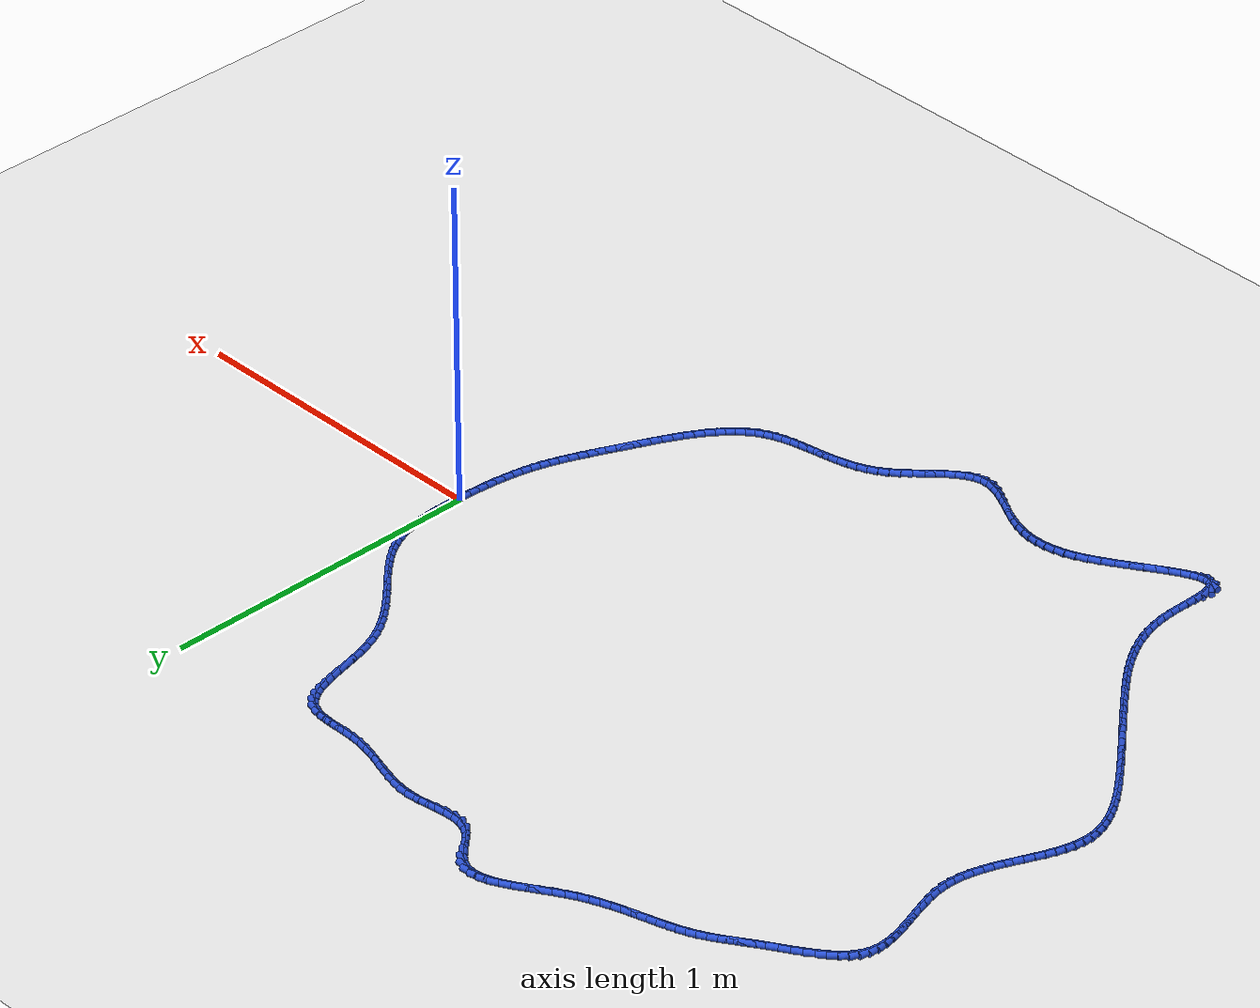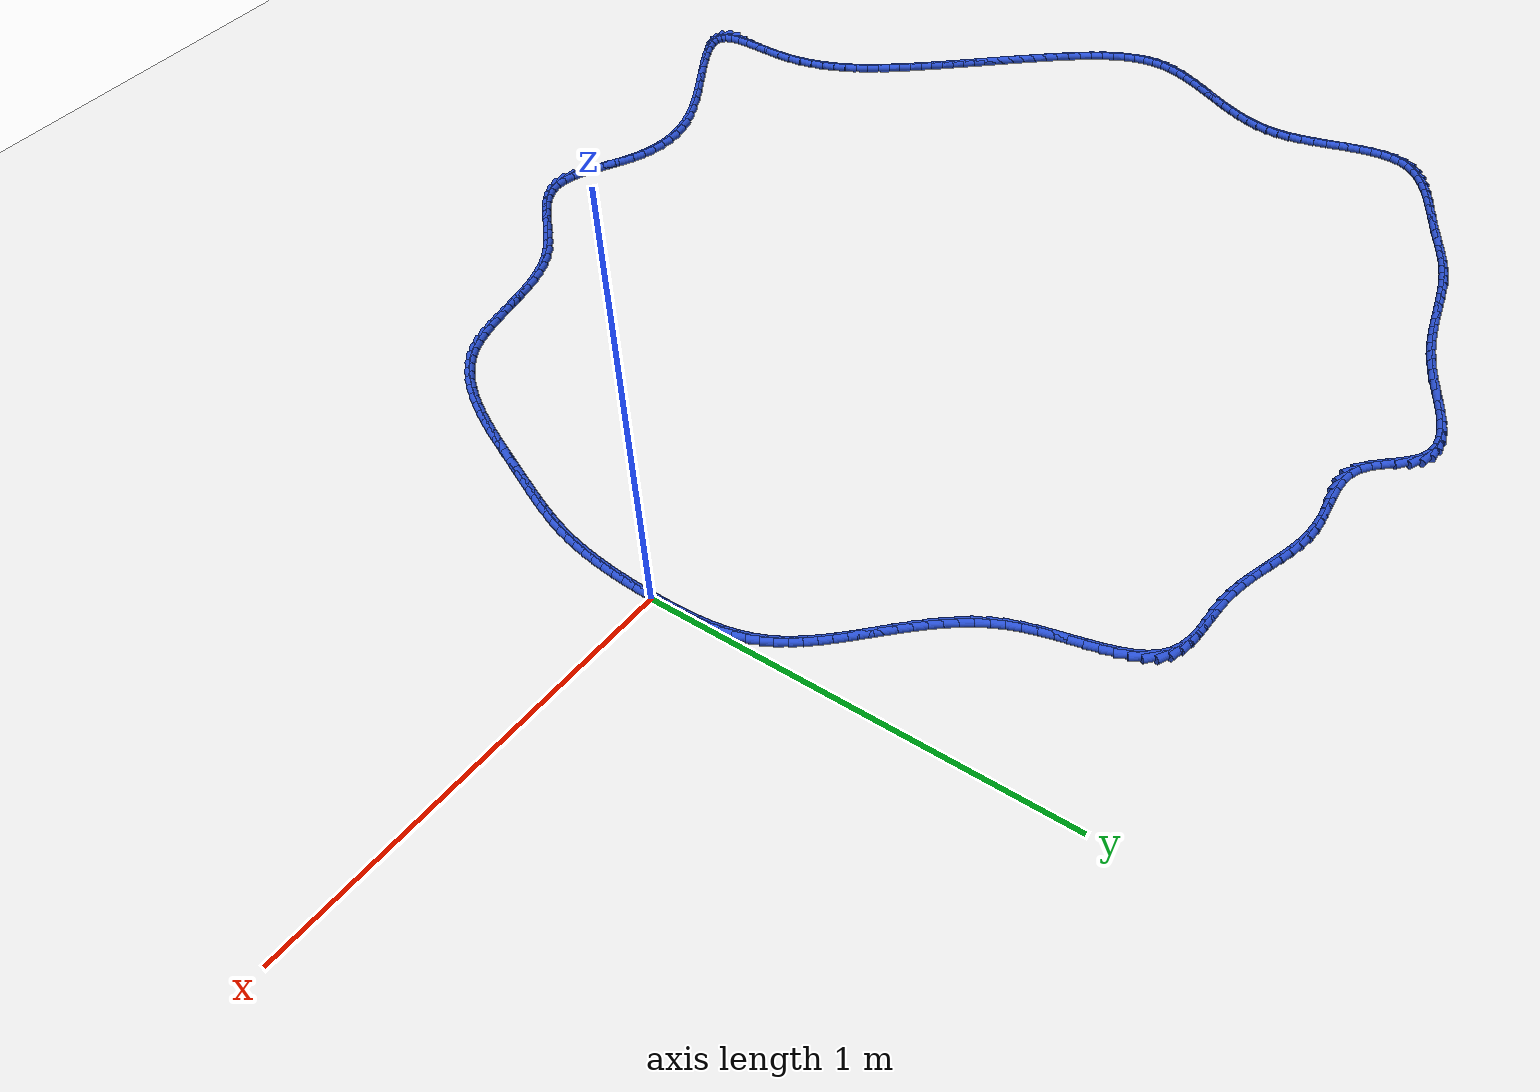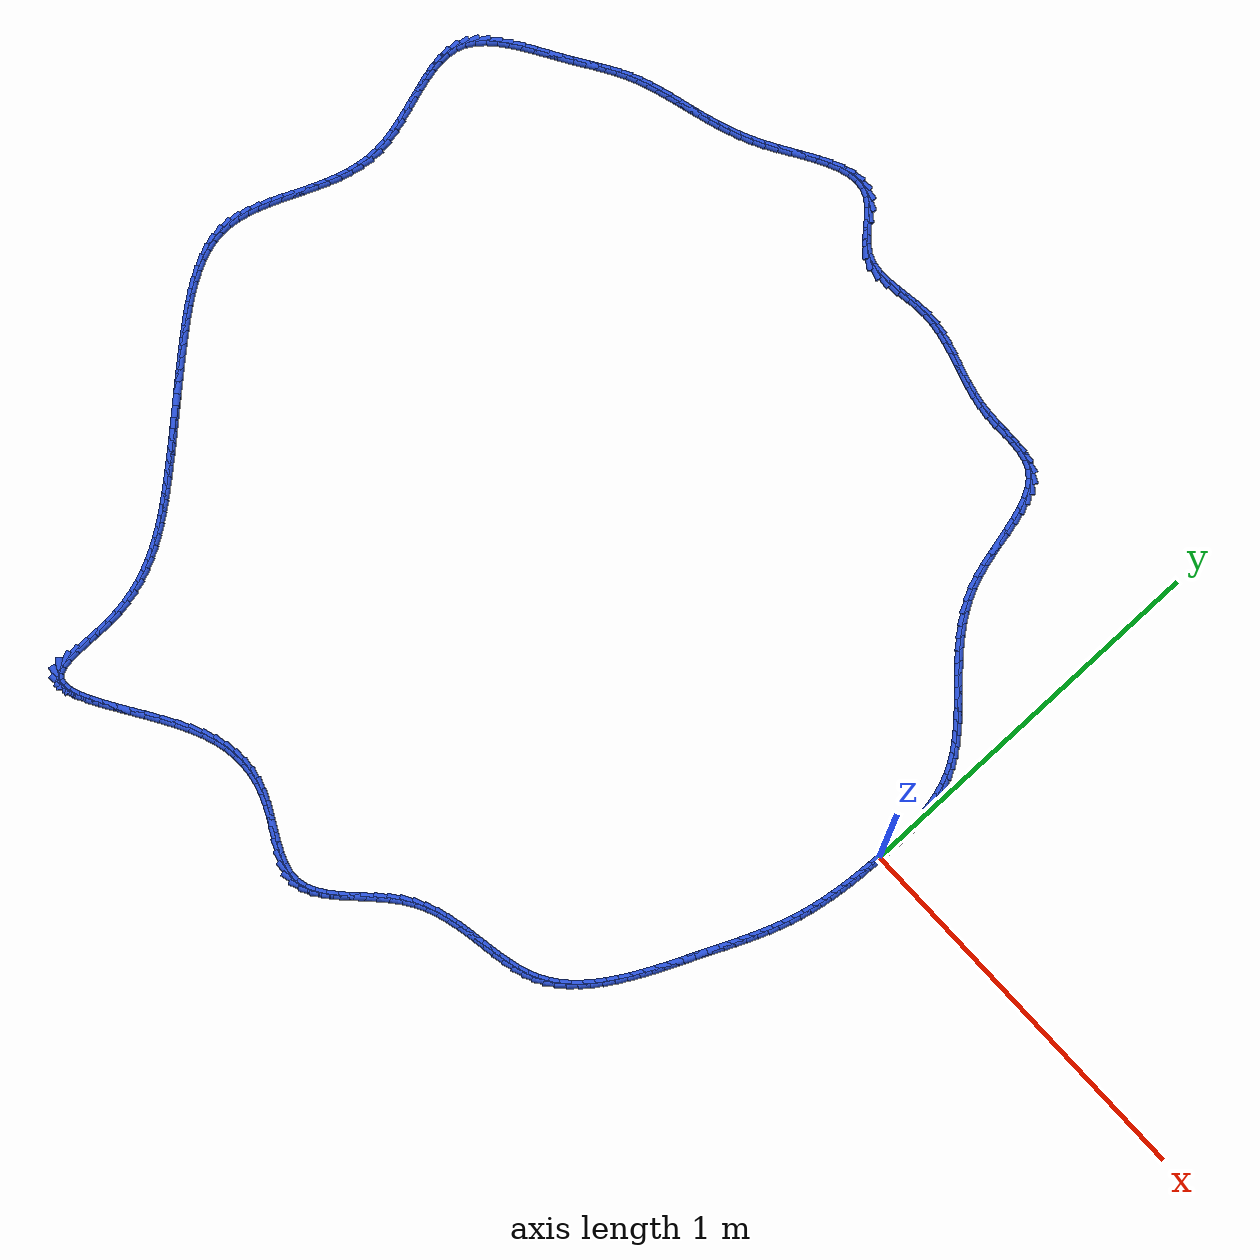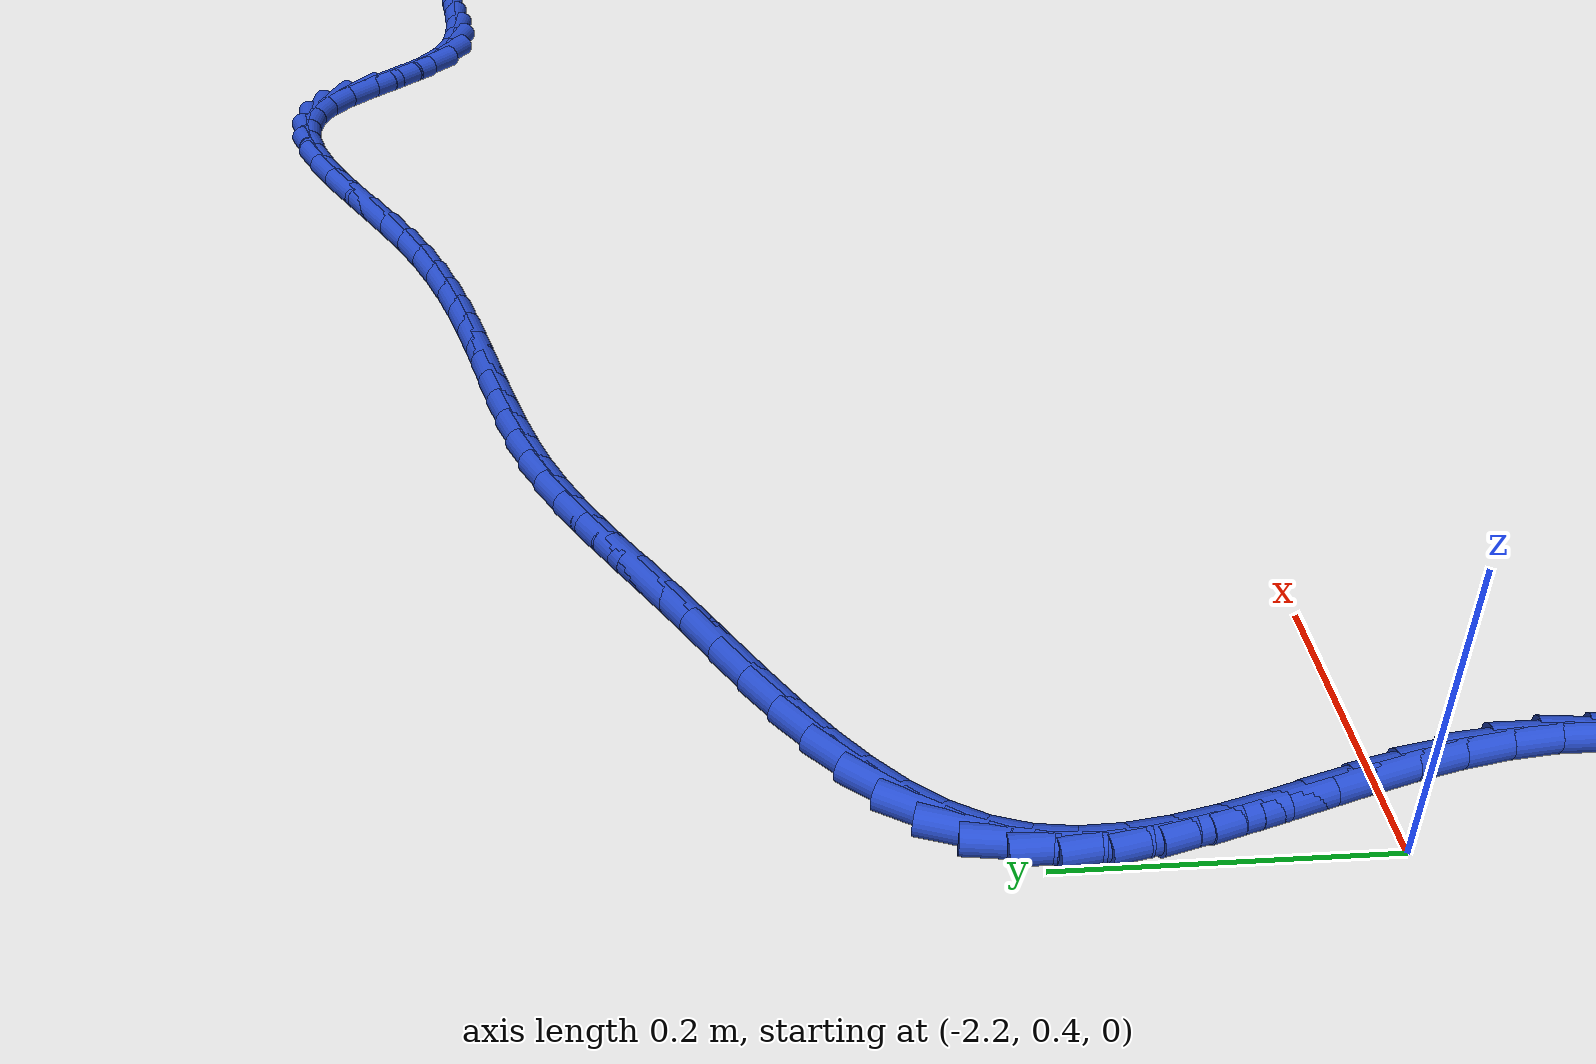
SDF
<sdf version="1.6">
 <world name="default">
  <light name="sun" type="directional">
   <pose>0 0 10 0 -0 0</pose>
   <diffuse>0.8 0.8 0.8 1</diffuse>
   <specular>0.2 0.2 0.2 1</specular>
   <attenuation>
    <range>1000</range>
    <constant>0.9</constant>
    <linear>0.01</linear>
    <quadratic>0.001</quadratic>
   </attenuation>
   <direction>-0.5 0.1 -0.9</direction>
  </light>
  <model name="ground_plane">
   <static>1</static>
   <link name="link">
    <collision name="collision">
     <geometry><plane><normal>0 0 1</normal><size>100 100</size></plane></geometry>
     <surface><friction><ode><mu>100</mu><mu2>50</mu2></ode></friction></surface>
    </collision>
    <visual name="visual">
     <cast_shadows>0</cast_shadows>
     <geometry><plane><normal>0 0 1</normal><size>100 100</size></plane></geometry>
     <material>
      <script><uri>file://media/materials/scripts/gazebo.material</uri><name>Gazebo/WhiteGlow</name></script>
     </material>
    </visual>
   </link>
  </model>
  <gravity>0 0 -9.8</gravity>
  <magnetic_field>6e-06 2.3e-05 -4.2e-05</magnetic_field>
  <atmosphere type="adiabatic"/>
  <physics name="default_physics" default="0" type="ode">
   <max_step_size>0.001</max_step_size>
   <real_time_factor>1</real_time_factor>
   <real_time_update_rate>1000</real_time_update_rate>
  </physics>
  <scene><ambient>0.4 0.4 0.4 1</ambient><background>0.7 0.7 0.7 1</background><shadows>1</shadows></scene>
  <spherical_coordinates>
   <surface_model>EARTH_WGS84</surface_model>
   <latitude_deg>0</latitude_deg>
   <longitude_deg>0</longitude_deg>
   <elevation>0</elevation>
   <heading_deg>0</heading_deg>
  </spherical_coordinates>
  <model name="line">
   <link name="link_0">
    <pose>-9.540979117872439e-18 -2.7755575615628914e-17 0.01 0 1.57 1.5484883831746084</pose>
    <collision name="collision">
     <geometry><cylinder><radius>0.01</radius><length>0.08</length></cylinder></geometry>
    </collision>
    <visual name="visual">
     <material>
      <script><name>Gazebo/Blue</name><uri>file://media/materials/scripts/gazebo.material</uri></script>
     </material>
     <geometry><cylinder><radius>0.01</radius><length>0.08</length></cylinder></geometry>
    </visual>
   </link>
   <link name="link_1">
    <pose>0.0006747044016769681 0.030240011742095913 0.01 0 1.57 1.5692283280628736</pose>
    <collision name="collision">
     <geometry><cylinder><radius>0.01</radius><length>0.08</length></cylinder></geometry>
    </collision>
    <visual name="visual">
     <material>
      <script><name>Gazebo/Blue</name><uri>file://media/materials/scripts/gazebo.material</uri></script>
     </material>
     <geometry><cylinder><radius>0.01</radius><length>0.08</length></cylinder></geometry>
    </visual>
   </link>
   <link name="link_2">
    <pose>0.000722217827271528 0.06054194100073871 0.01 0 1.57 -1.5439458558823596</pose>
    <collision name="collision">
     <geometry><cylinder><radius>0.01</radius><length>0.08</length></cylinder></geometry>
    </collision>
    <visual name="visual">
     <material>
      <script><name>Gazebo/Blue</name><uri>file://media/materials/scripts/gazebo.material</uri></script>
     </material>
     <geometry><cylinder><radius>0.01</radius><length>0.08</length></cylinder></geometry>
    </visual>
   </link>
   <link name="link_3">
    <pose>-8.813932358002659e-05 0.09071505797876772 0.01 0 1.57 -1.5072745340165148</pose>
    <collision name="collision">
     <geometry><cylinder><radius>0.01</radius><length>0.08</length></cylinder></geometry>
    </collision>
    <visual name="visual">
     <material>
      <script><name>Gazebo/Blue</name><uri>file://media/materials/scripts/gazebo.material</uri></script>
     </material>
     <geometry><cylinder><radius>0.01</radius><length>0.08</length></cylinder></geometry>
    </visual>
   </link>
   <link name="link_4">
    <pose>-0.001987046651241392 0.12056863287902227 0.01 0 1.57 -1.461560944917181</pose>
    <collision name="collision">
     <geometry><cylinder><radius>0.01</radius><length>0.08</length></cylinder></geometry>
    </collision>
    <visual name="visual">
     <material>
      <script><name>Gazebo/Blue</name><uri>file://media/materials/scripts/gazebo.material</uri></script>
     </material>
     <geometry><cylinder><radius>0.01</radius><length>0.08</length></cylinder></geometry>
    </visual>
   </link>
   <link name="link_5">
    <pose>-0.005205183756076266 0.14991193590434168 0.01 0 1.57 -1.4058402781953563</pose>
    <collision name="collision">
     <geometry><cylinder><radius>0.01</radius><length>0.08</length></cylinder></geometry>
    </collision>
    <visual name="visual">
     <material>
      <script><name>Gazebo/Blue</name><uri>file://media/materials/scripts/gazebo.material</uri></script>
     </material>
     <geometry><cylinder><radius>0.01</radius><length>0.08</length></cylinder></geometry>
    </visual>
   </link>
   <link name="link_6">
    <pose>-0.009973230238448347 0.17855423725756528 0.01 0 1.57 -1.339053946603382</pose>
    <collision name="collision">
     <geometry><cylinder><radius>0.01</radius><length>0.08</length></cylinder></geometry>
    </collision>
    <visual name="visual">
     <material>
      <script><name>Gazebo/Blue</name><uri>file://media/materials/scripts/gazebo.material</uri></script>
     </material>
     <geometry><cylinder><radius>0.01</radius><length>0.08</length></cylinder></geometry>
    </visual>
   </link>
   <link name="link_7">
    <pose>-0.016521865698721327 0.2063048071415322 0.01 0 1.57 -1.2602055314917822</pose>
    <collision name="collision">
     <geometry><cylinder><radius>0.01</radius><length>0.08</length></cylinder></geometry>
    </collision>
    <visual name="visual">
     <material>
      <script><name>Gazebo/Blue</name><uri>file://media/materials/scripts/gazebo.material</uri></script>
     </material>
     <geometry><cylinder><radius>0.01</radius><length>0.08</length></cylinder></geometry>
    </visual>
   </link>
   <link name="link_8">
    <pose>-0.025081769737258914 0.23297291575908202 0.01 0 1.57 -1.1688429636531577</pose>
    <collision name="collision">
     <geometry><cylinder><radius>0.01</radius><length>0.08</length></cylinder></geometry>
    </collision>
    <visual name="visual">
     <material>
      <script><name>Gazebo/Blue</name><uri>file://media/materials/scripts/gazebo.material</uri></script>
     </material>
     <geometry><cylinder><radius>0.01</radius><length>0.08</length></cylinder></geometry>
    </visual>
   </link>
   <link name="link_9">
    <pose>-0.03587869097670112 0.2583716000240663 0.01 0 1.57 -1.0744107391107462</pose>
    <collision name="collision">
     <geometry><cylinder><radius>0.01</radius><length>0.08</length></cylinder></geometry>
    </collision>
    <visual name="visual">
     <material>
      <script><name>Gazebo/Blue</name><uri>file://media/materials/scripts/gazebo.material</uri></script>
     </material>
     <geometry><cylinder><radius>0.01</radius><length>0.08</length></cylinder></geometry>
    </visual>
   </link>
   <link name="link_10">
    <pose>-0.0489317666691276 0.28247172464197645 0.01 0 1.57 -0.9910271843023188</pose>
    <collision name="collision">
     <geometry><cylinder><radius>0.01</radius><length>0.08</length></cylinder></geometry>
    </collision>
    <visual name="visual">
     <material>
      <script><name>Gazebo/Blue</name><uri>file://media/materials/scripts/gazebo.material</uri></script>
     </material>
     <geometry><cylinder><radius>0.01</radius><length>0.08</length></cylinder></geometry>
    </visual>
   </link>
   <link name="link_11">
    <pose>-0.06398277350245637 0.3054560265168717 0.01 0 1.57 -0.9208965060991512</pose>
    <collision name="collision">
     <geometry><cylinder><radius>0.01</radius><length>0.08</length></cylinder></geometry>
    </collision>
    <visual name="visual">
     <material>
      <script><name>Gazebo/Blue</name><uri>file://media/materials/scripts/gazebo.material</uri></script>
     </material>
     <geometry><cylinder><radius>0.01</radius><length>0.08</length></cylinder></geometry>
    </visual>
   </link>
   <link name="link_12">
    <pose>-0.08075402157961464 0.32752211282888294 0.01 0 1.57 -0.8643976082467374</pose>
    <collision name="collision">
     <geometry><cylinder><radius>0.01</radius><length>0.08</length></cylinder></geometry>
    </collision>
    <visual name="visual">
     <material>
      <script><name>Gazebo/Blue</name><uri>file://media/materials/scripts/gazebo.material</uri></script>
     </material>
     <geometry><cylinder><radius>0.01</radius><length>0.08</length></cylinder></geometry>
    </visual>
   </link>
   <link name="link_13">
    <pose>-0.09896782100352962 0.3488675907581414 0.01 0 1.57 -0.8212975343984538</pose>
    <collision name="collision">
     <geometry><cylinder><radius>0.01</radius><length>0.08</length></cylinder></geometry>
    </collision>
    <visual name="visual">
     <material>
      <script><name>Gazebo/Blue</name><uri>file://media/materials/scripts/gazebo.material</uri></script>
     </material>
     <geometry><cylinder><radius>0.01</radius><length>0.08</length></cylinder></geometry>
    </visual>
   </link>
   <link name="link_14">
    <pose>-0.11834648187712847 0.36969006748477834 0.01 0 1.57 -0.7910711579913317</pose>
    <collision name="collision">
     <geometry><cylinder><radius>0.01</radius><length>0.08</length></cylinder></geometry>
    </collision>
    <visual name="visual">
     <material>
      <script><name>Gazebo/Blue</name><uri>file://media/materials/scripts/gazebo.material</uri></script>
     </material>
     <geometry><cylinder><radius>0.01</radius><length>0.08</length></cylinder></geometry>
    </visual>
   </link>
   <link name="link_15">
    <pose>-0.13861231430333837 0.3901871501889247 0.01 0 1.57 -0.7731300674181292</pose>
    <collision name="collision">
     <geometry><cylinder><radius>0.01</radius><length>0.08</length></cylinder></geometry>
    </collision>
    <visual name="visual">
     <material>
      <script><name>Gazebo/Blue</name><uri>file://media/materials/scripts/gazebo.material</uri></script>
     </material>
     <geometry><cylinder><radius>0.01</radius><length>0.08</length></cylinder></geometry>
    </visual>
   </link>
   <link name="link_16">
    <pose>-0.15948762838508665 0.4105564460507118 0.01 0 1.57 -0.7669594535739842</pose>
    <collision name="collision">
     <geometry><cylinder><radius>0.01</radius><length>0.08</length></cylinder></geometry>
    </collision>
    <visual name="visual">
     <material>
      <script><name>Gazebo/Blue</name><uri>file://media/materials/scripts/gazebo.material</uri></script>
     </material>
     <geometry><cylinder><radius>0.01</radius><length>0.08</length></cylinder></geometry>
    </visual>
   </link>
   <link name="link_17">
    <pose>-0.18069473422530036 0.4309955622502707 0.01 0 1.57 -0.7721824996168228</pose>
    <collision name="collision">
     <geometry><cylinder><radius>0.01</radius><length>0.08</length></cylinder></geometry>
    </collision>
    <visual name="visual">
     <material>
      <script><name>Gazebo/Blue</name><uri>file://media/materials/scripts/gazebo.material</uri></script>
     </material>
     <geometry><cylinder><radius>0.01</radius><length>0.08</length></cylinder></geometry>
    </visual>
   </link>
   <link name="link_18">
    <pose>-0.20195594192690672 0.45170210596773264 0.01 0 1.57 -0.7885718389445868</pose>
    <collision name="collision">
     <geometry><cylinder><radius>0.01</radius><length>0.08</length></cylinder></geometry>
    </collision>
    <visual name="visual">
     <material>
      <script><name>Gazebo/Blue</name><uri>file://media/materials/scripts/gazebo.material</uri></script>
     </material>
     <geometry><cylinder><radius>0.01</radius><length>0.08</length></cylinder></geometry>
    </visual>
   </link>
   <link name="link_19">
    <pose>-0.2229935615928329 0.4728736843832283 0.01 0 1.57 -0.8160201989703334</pose>
    <collision name="collision">
     <geometry><cylinder><radius>0.01</radius><length>0.08</length></cylinder></geometry>
    </collision>
    <visual name="visual">
     <material>
      <script><name>Gazebo/Blue</name><uri>file://media/materials/scripts/gazebo.material</uri></script>
     </material>
     <geometry><cylinder><radius>0.01</radius><length>0.08</length></cylinder></geometry>
    </visual>
   </link>
   <link name="link_20">
    <pose>-0.24352990332600627 0.4947079046768894 0.01 0 1.57 -0.8544746093773524</pose>
    <collision name="collision">
     <geometry><cylinder><radius>0.01</radius><length>0.08</length></cylinder></geometry>
    </collision>
    <visual name="visual">
     <material>
      <script><name>Gazebo/Blue</name><uri>file://media/materials/scripts/gazebo.material</uri></script>
     </material>
     <geometry><cylinder><radius>0.01</radius><length>0.08</length></cylinder></geometry>
    </visual>
   </link>
   <link name="link_21">
    <pose>-0.26328727722935386 0.5174023740288467 0.01 0 1.57 -0.9038341413493509</pose>
    <collision name="collision">
     <geometry><cylinder><radius>0.01</radius><length>0.08</length></cylinder></geometry>
    </collision>
    <visual name="visual">
     <material>
      <script><name>Gazebo/Blue</name><uri>file://media/materials/scripts/gazebo.material</uri></script>
     </material>
     <geometry><cylinder><radius>0.01</radius><length>0.08</length></cylinder></geometry>
    </visual>
   </link>
   <link name="link_22">
    <pose>-0.28198799340580283 0.5411546996192315 0.01 0 1.57 -0.9638127523560778</pose>
    <collision name="collision">
     <geometry><cylinder><radius>0.01</radius><length>0.08</length></cylinder></geometry>
    </collision>
    <visual name="visual">
     <material>
      <script><name>Gazebo/Blue</name><uri>file://media/materials/scripts/gazebo.material</uri></script>
     </material>
     <geometry><cylinder><radius>0.01</radius><length>0.08</length></cylinder></geometry>
    </visual>
   </link>
   <link name="link_23">
    <pose>-0.29935436195828063 0.5661624886281751 0.01 0 1.57 -1.0337790124388864</pose>
    <collision name="collision">
     <geometry><cylinder><radius>0.01</radius><length>0.08</length></cylinder></geometry>
    </collision>
    <visual name="visual">
     <material>
      <script><name>Gazebo/Blue</name><uri>file://media/materials/scripts/gazebo.material</uri></script>
     </material>
     <geometry><cylinder><radius>0.01</radius><length>0.08</length></cylinder></geometry>
    </visual>
   </link>
   <link name="link_24">
    <pose>-0.31510869298971417 0.5926233482358081 0.01 0 1.57 -1.1126036904272005</pose>
    <collision name="collision">
     <geometry><cylinder><radius>0.01</radius><length>0.08</length></cylinder></geometry>
    </collision>
    <visual name="visual">
     <material>
      <script><name>Gazebo/Blue</name><uri>file://media/materials/scripts/gazebo.material</uri></script>
     </material>
     <geometry><cylinder><radius>0.01</radius><length>0.08</length></cylinder></geometry>
    </visual>
   </link>
   <link name="link_25">
    <pose>-0.3289732966030309 0.6207348856222621 0.01 0 1.57 -1.1969932518566078</pose>
    <collision name="collision">
     <geometry><cylinder><radius>0.01</radius><length>0.08</length></cylinder></geometry>
    </collision>
    <visual name="visual">
     <material>
      <script><name>Gazebo/Blue</name><uri>file://media/materials/scripts/gazebo.material</uri></script>
     </material>
     <geometry><cylinder><radius>0.01</radius><length>0.08</length></cylinder></geometry>
    </visual>
   </link>
   <link name="link_26">
    <pose>-0.34070950662291455 0.6506555081581253 0.01 0 1.57 -1.2668179192720221</pose>
    <collision name="collision">
     <geometry><cylinder><radius>0.01</radius><length>0.08</length></cylinder></geometry>
    </collision>
    <visual name="visual">
     <material>
      <script><name>Gazebo/Blue</name><uri>file://media/materials/scripts/gazebo.material</uri></script>
     </material>
     <geometry><cylinder><radius>0.01</radius><length>0.08</length></cylinder></geometry>
    </visual>
   </link>
   <link name="link_27">
    <pose>-0.35056087664897395 0.6820592275058446 0.01 0 1.57 -1.3119455169228171</pose>
    <collision name="collision">
     <geometry><cylinder><radius>0.01</radius><length>0.08</length></cylinder></geometry>
    </collision>
    <visual name="visual">
     <material>
      <script><name>Gazebo/Blue</name><uri>file://media/materials/scripts/gazebo.material</uri></script>
     </material>
     <geometry><cylinder><radius>0.01</radius><length>0.08</length></cylinder></geometry>
    </visual>
   </link>
   <link name="link_28">
    <pose>-0.3590961957406196 0.7142933522993802 0.01 0 1.57 -1.334761892262461</pose>
    <collision name="collision">
     <geometry><cylinder><radius>0.01</radius><length>0.08</length></cylinder></geometry>
    </collision>
    <visual name="visual">
     <material>
      <script><name>Gazebo/Blue</name><uri>file://media/materials/scripts/gazebo.material</uri></script>
     </material>
     <geometry><cylinder><radius>0.01</radius><length>0.08</length></cylinder></geometry>
    </visual>
   </link>
   <link name="link_29">
    <pose>-0.36689034504589085 0.7466990715945689 0.01 0 1.57 -1.3362167028174856</pose>
    <collision name="collision">
     <geometry><cylinder><radius>0.01</radius><length>0.08</length></cylinder></geometry>
    </collision>
    <visual name="visual">
     <material>
      <script><name>Gazebo/Blue</name><uri>file://media/materials/scripts/gazebo.material</uri></script>
     </material>
     <geometry><cylinder><radius>0.01</radius><length>0.08</length></cylinder></geometry>
    </visual>
   </link>
   <link name="link_30">
    <pose>-0.3745182057128275 0.7786175744472477 0.01 0 1.57 -1.315344658231414</pose>
    <collision name="collision">
     <geometry><cylinder><radius>0.01</radius><length>0.08</length></cylinder></geometry>
    </collision>
    <visual name="visual">
     <material>
      <script><name>Gazebo/Blue</name><uri>file://media/materials/scripts/gazebo.material</uri></script>
     </material>
     <geometry><cylinder><radius>0.01</radius><length>0.08</length></cylinder></geometry>
    </visual>
   </link>
   <link name="link_31">
    <pose>-0.382554658889469 0.8093900499132529 0.01 0 1.57 -1.2689326434410981</pose>
    <collision name="collision">
     <geometry><cylinder><radius>0.01</radius><length>0.08</length></cylinder></geometry>
    </collision>
    <visual name="visual">
     <material>
      <script><name>Gazebo/Blue</name><uri>file://media/materials/scripts/gazebo.material</uri></script>
     </material>
     <geometry><cylinder><radius>0.01</radius><length>0.08</length></cylinder></geometry>
    </visual>
   </link>
   <link name="link_32">
    <pose>-0.39157458572385495 0.8383576870484215 0.01 0 1.57 -1.1910484748648047</pose>
    <collision name="collision">
     <geometry><cylinder><radius>0.01</radius><length>0.08</length></cylinder></geometry>
    </collision>
    <visual name="visual">
     <material>
      <script><name>Gazebo/Blue</name><uri>file://media/materials/scripts/gazebo.material</uri></script>
     </material>
     <geometry><cylinder><radius>0.01</radius><length>0.08</length></cylinder></geometry>
    </visual>
   </link>
   <link name="link_33">
    <pose>-0.40215286736402484 0.86486167490859 0.01 0 1.57 -1.07283646956556</pose>
    <collision name="collision">
     <geometry><cylinder><radius>0.01</radius><length>0.08</length></cylinder></geometry>
    </collision>
    <visual name="visual">
     <material>
      <script><name>Gazebo/Blue</name><uri>file://media/materials/scripts/gazebo.material</uri></script>
     </material>
     <geometry><cylinder><radius>0.01</radius><length>0.08</length></cylinder></geometry>
    </visual>
   </link>
   <link name="link_34">
    <pose>-0.4148643849580185 0.8882432025495953 0.01 0 1.57 -0.9042143586479815</pose>
    <collision name="collision">
     <geometry><cylinder><radius>0.01</radius><length>0.08</length></cylinder></geometry>
    </collision>
    <visual name="visual">
     <material>
      <script><name>Gazebo/Blue</name><uri>file://media/materials/scripts/gazebo.material</uri></script>
     </material>
     <geometry><cylinder><radius>0.01</radius><length>0.08</length></cylinder></geometry>
    </visual>
   </link>
   <link name="link_35">
    <pose>-0.4302840196538752 0.9078434590272739 0.01 0 1.57 -0.681165214891603</pose>
    <collision name="collision">
     <geometry><cylinder><radius>0.01</radius><length>0.08</length></cylinder></geometry>
    </collision>
    <visual name="visual">
     <material>
      <script><name>Gazebo/Blue</name><uri>file://media/materials/scripts/gazebo.material</uri></script>
     </material>
     <geometry><cylinder><radius>0.01</radius><length>0.08</length></cylinder></geometry>
    </visual>
   </link>
   <link name="link_36">
    <pose>-0.4489866525996346 0.9230036333974625 0.01 0 1.57 -0.4230516756560272</pose>
    <collision name="collision">
     <geometry><cylinder><radius>0.01</radius><length>0.08</length></cylinder></geometry>
    </collision>
    <visual name="visual">
     <material>
      <script><name>Gazebo/Blue</name><uri>file://media/materials/scripts/gazebo.material</uri></script>
     </material>
     <geometry><cylinder><radius>0.01</radius><length>0.08</length></cylinder></geometry>
    </visual>
   </link>
   <link name="link_37">
    <pose>-0.4714944790223623 0.9331375079856906 0.01 0 1.57 -0.21220910343965724</pose>
    <collision name="collision">
     <geometry><cylinder><radius>0.01</radius><length>0.08</length></cylinder></geometry>
    </collision>
    <visual name="visual">
     <material>
      <script><name>Gazebo/Blue</name><uri>file://media/materials/scripts/gazebo.material</uri></script>
     </material>
     <geometry><cylinder><radius>0.01</radius><length>0.08</length></cylinder></geometry>
    </visual>
   </link>
   <link name="link_38">
    <pose>-0.49753865137191267 0.9387488030098703 0.01 0 1.57 -0.08458062376592698</pose>
    <collision name="collision">
     <geometry><cylinder><radius>0.01</radius><length>0.08</length></cylinder></geometry>
    </collision>
    <visual name="visual">
     <material>
      <script><name>Gazebo/Blue</name><uri>file://media/materials/scripts/gazebo.material</uri></script>
     </material>
     <geometry><cylinder><radius>0.01</radius><length>0.08</length></cylinder></geometry>
    </visual>
   </link>
   <link name="link_39">
    <pose>-0.526239989212518 0.9411821855471357 0.01 0 1.57 -0.020411069244320162</pose>
    <collision name="collision">
     <geometry><cylinder><radius>0.01</radius><length>0.08</length></cylinder></geometry>
    </collision>
    <visual name="visual">
     <material>
      <script><name>Gazebo/Blue</name><uri>file://media/materials/scripts/gazebo.material</uri></script>
     </material>
     <geometry><cylinder><radius>0.01</radius><length>0.08</length></cylinder></geometry>
    </visual>
   </link>
   <link name="link_40">
    <pose>-0.5567035319266505 0.941804065390116 0.01 0 1.57 -0.0056425350980393455</pose>
    <collision name="collision">
     <geometry><cylinder><radius>0.01</radius><length>0.08</length></cylinder></geometry>
    </collision>
    <visual name="visual">
     <material>
      <script><name>Gazebo/Blue</name><uri>file://media/materials/scripts/gazebo.material</uri></script>
     </material>
     <geometry><cylinder><radius>0.01</radius><length>0.08</length></cylinder></geometry>
    </visual>
   </link>
   <link name="link_41">
    <pose>-0.5880343188967821 0.9419808523314409 0.01 0 1.57 -0.03506536915329375</pose>
    <collision name="collision">
     <geometry><cylinder><radius>0.01</radius><length>0.08</length></cylinder></geometry>
    </collision>
    <visual name="visual">
     <material>
      <script><name>Gazebo/Blue</name><uri>file://media/materials/scripts/gazebo.material</uri></script>
     </material>
     <geometry><cylinder><radius>0.01</radius><length>0.08</length></cylinder></geometry>
    </visual>
   </link>
   <link name="link_42">
    <pose>-0.6193373895053849 0.9430789561637389 0.01 0 1.57 -0.10591906895784575</pose>
    <collision name="collision">
     <geometry><cylinder><radius>0.01</radius><length>0.08</length></cylinder></geometry>
    </collision>
    <visual name="visual">
     <material>
      <script><name>Gazebo/Blue</name><uri>file://media/materials/scripts/gazebo.material</uri></script>
     </material>
     <geometry><cylinder><radius>0.01</radius><length>0.08</length></cylinder></geometry>
    </visual>
   </link>
   <link name="link_43">
    <pose>-0.6498006407114233 0.9463177161571921 0.01 0 1.57 -0.18078344644667094</pose>
    <collision name="collision">
     <geometry><cylinder><radius>0.01</radius><length>0.08</length></cylinder></geometry>
    </collision>
    <visual name="visual">
     <material>
      <script><name>Gazebo/Blue</name><uri>file://media/materials/scripts/gazebo.material</uri></script>
     </material>
     <geometry><cylinder><radius>0.01</radius><length>0.08</length></cylinder></geometry>
    </visual>
   </link>
   <link name="link_44">
    <pose>-0.679292670590668 0.9517082408670838 0.01 0 1.57 -0.23774428302720194</pose>
    <collision name="collision">
     <geometry><cylinder><radius>0.01</radius><length>0.08</length></cylinder></geometry>
    </collision>
    <visual name="visual">
     <material>
      <script><name>Gazebo/Blue</name><uri>file://media/materials/scripts/gazebo.material</uri></script>
     </material>
     <geometry><cylinder><radius>0.01</radius><length>0.08</length></cylinder></geometry>
    </visual>
   </link>
   <link name="link_45">
    <pose>-0.7080161226382938 0.9586687149854519 0.01 0 1.57 -0.2749756630033735</pose>
    <collision name="collision">
     <geometry><cylinder><radius>0.01</radius><length>0.08</length></cylinder></geometry>
    </collision>
    <visual name="visual">
     <material>
      <script><name>Gazebo/Blue</name><uri>file://media/materials/scripts/gazebo.material</uri></script>
     </material>
     <geometry><cylinder><radius>0.01</radius><length>0.08</length></cylinder></geometry>
    </visual>
   </link>
   <link name="link_46">
    <pose>-0.7361759462146648 0.9666132303402589 0.01 0 1.57 -0.291532859822424</pose>
    <collision name="collision">
     <geometry><cylinder><radius>0.01</radius><length>0.08</length></cylinder></geometry>
    </collision>
    <visual name="visual">
     <material>
      <script><name>Gazebo/Blue</name><uri>file://media/materials/scripts/gazebo.material</uri></script>
     </material>
     <geometry><cylinder><radius>0.01</radius><length>0.08</length></cylinder></geometry>
    </visual>
   </link>
   <link name="link_47">
    <pose>-0.7639770906801445 0.9749558787594681 0.01 0 1.57 -0.2868262808259433</pose>
    <collision name="collision">
     <geometry><cylinder><radius>0.01</radius><length>0.08</length></cylinder></geometry>
    </collision>
    <visual name="visual">
     <material>
      <script><name>Gazebo/Blue</name><uri>file://media/materials/scripts/gazebo.material</uri></script>
     </material>
     <geometry><cylinder><radius>0.01</radius><length>0.08</length></cylinder></geometry>
    </visual>
   </link>
   <link name="link_48">
    <pose>-0.7916245053950974 0.983110752071042 0.01 0 1.57 -0.26043006347054515</pose>
    <collision name="collision">
     <geometry><cylinder><radius>0.01</radius><length>0.08</length></cylinder></geometry>
    </collision>
    <visual name="visual">
     <material>
      <script><name>Gazebo/Blue</name><uri>file://media/materials/scripts/gazebo.material</uri></script>
     </material>
     <geometry><cylinder><radius>0.01</radius><length>0.08</length></cylinder></geometry>
    </visual>
   </link>
   <link name="link_49">
    <pose>-0.8193231397198877 0.9904919421029437 0.01 0 1.57 -0.21216303472597392</pose>
    <collision name="collision">
     <geometry><cylinder><radius>0.01</radius><length>0.08</length></cylinder></geometry>
    </collision>
    <visual name="visual">
     <material>
      <script><name>Gazebo/Blue</name><uri>file://media/materials/scripts/gazebo.material</uri></script>
     </material>
     <geometry><cylinder><radius>0.01</radius><length>0.08</length></cylinder></geometry>
    </visual>
   </link>
   <link name="link_50">
    <pose>-0.8472779430148787 0.9965135406831352 0.01 0 1.57 -0.14247231676425356</pose>
    <collision name="collision">
     <geometry><cylinder><radius>0.01</radius><length>0.08</length></cylinder></geometry>
    </collision>
    <visual name="visual">
     <material>
      <script><name>Gazebo/Blue</name><uri>file://media/materials/scripts/gazebo.material</uri></script>
     </material>
     <geometry><cylinder><radius>0.01</radius><length>0.08</length></cylinder></geometry>
    </visual>
   </link>
   <link name="link_51">
    <pose>-0.8756938646404349 1.0005896396395801 0.01 0 1.57 -0.053065179488171424</pose>
    <collision name="collision">
     <geometry><cylinder><radius>0.01</radius><length>0.08</length></cylinder></geometry>
    </collision>
    <visual name="visual">
     <material>
      <script><name>Gazebo/Blue</name><uri>file://media/materials/scripts/gazebo.material</uri></script>
     </material>
     <geometry><cylinder><radius>0.01</radius><length>0.08</length></cylinder></geometry>
    </visual>
   </link>
   <link name="link_52">
    <pose>-0.9047758539569197 1.0021343308002406 0.01 0 1.57 0.049674849690453465</pose>
    <collision name="collision">
     <geometry><cylinder><radius>0.01</radius><length>0.08</length></cylinder></geometry>
    </collision>
    <visual name="visual">
     <material>
      <script><name>Gazebo/Blue</name><uri>file://media/materials/scripts/gazebo.material</uri></script>
     </material>
     <geometry><cylinder><radius>0.01</radius><length>0.08</length></cylinder></geometry>
    </visual>
   </link>
   <link name="link_53">
    <pose>-0.934701137583983 1.0006465729069214 0.01 0 1.57 0.12389733416307588</pose>
    <collision name="collision">
     <geometry><cylinder><radius>0.01</radius><length>0.08</length></cylinder></geometry>
    </collision>
    <visual name="visual">
     <material>
      <script><name>Gazebo/Blue</name><uri>file://media/materials/scripts/gazebo.material</uri></script>
     </material>
     <geometry><cylinder><radius>0.01</radius><length>0.08</length></cylinder></geometry>
    </visual>
   </link>
   <link name="link_54">
    <pose>-0.9652494244393475 0.996842235428494 0.01 0 1.57 0.1455890739950447</pose>
    <collision name="collision">
     <geometry><cylinder><radius>0.01</radius><length>0.08</length></cylinder></geometry>
    </collision>
    <visual name="visual">
     <material>
      <script><name>Gazebo/Blue</name><uri>file://media/materials/scripts/gazebo.material</uri></script>
     </material>
     <geometry><cylinder><radius>0.01</radius><length>0.08</length></cylinder></geometry>
    </visual>
   </link>
   <link name="link_55">
    <pose>-0.995903025420873 0.9923476047506802 0.01 0 1.57 0.11644786413394823</pose>
    <collision name="collision">
     <geometry><cylinder><radius>0.01</radius><length>0.08</length></cylinder></geometry>
    </collision>
    <visual name="visual">
     <material>
      <script><name>Gazebo/Blue</name><uri>file://media/materials/scripts/gazebo.material</uri></script>
     </material>
     <geometry><cylinder><radius>0.01</radius><length>0.08</length></cylinder></geometry>
    </visual>
   </link>
   <link name="link_56">
    <pose>-1.0261370826259053 0.9888109129240193 0.01 0 1.57 0.03175892774925111</pose>
    <collision name="collision">
     <geometry><cylinder><radius>0.01</radius><length>0.08</length></cylinder></geometry>
    </collision>
    <visual name="visual">
     <material>
      <script><name>Gazebo/Blue</name><uri>file://media/materials/scripts/gazebo.material</uri></script>
     </material>
     <geometry><cylinder><radius>0.01</radius><length>0.08</length></cylinder></geometry>
    </visual>
   </link>
   <link name="link_57">
    <pose>-1.05542673815179 0.9878803919990511 0.01 0 1.57 -0.11891277202247175</pose>
    <collision name="collision">
     <geometry><cylinder><radius>0.01</radius><length>0.08</length></cylinder></geometry>
    </collision>
    <visual name="visual">
     <material>
      <script><name>Gazebo/Blue</name><uri>file://media/materials/scripts/gazebo.material</uri></script>
     </material>
     <geometry><cylinder><radius>0.01</radius><length>0.08</length></cylinder></geometry>
    </visual>
   </link>
   <link name="link_58">
    <pose>-1.083247134095873 0.9912042740263156 0.01 0 1.57 -0.34312167423232015</pose>
    <collision name="collision">
     <geometry><cylinder><radius>0.01</radius><length>0.08</length></cylinder></geometry>
    </collision>
    <visual name="visual">
     <material>
      <script><name>Gazebo/Blue</name><uri>file://media/materials/scripts/gazebo.material</uri></script>
     </material>
     <geometry><cylinder><radius>0.01</radius><length>0.08</length></cylinder></geometry>
    </visual>
   </link>
   <link name="link_59">
    <pose>-1.1090734125554993 1.0004307910563526 0.01 0 1.57 -0.6023063651892756</pose>
    <collision name="collision">
     <geometry><cylinder><radius>0.01</radius><length>0.08</length></cylinder></geometry>
    </collision>
    <visual name="visual">
     <material>
      <script><name>Gazebo/Blue</name><uri>file://media/materials/scripts/gazebo.material</uri></script>
     </material>
     <geometry><cylinder><radius>0.01</radius><length>0.08</length></cylinder></geometry>
    </visual>
   </link>
   <link name="link_60">
    <pose>-1.1325612132692755 1.016579311914428 0.01 0 1.57 -0.7668667659744497</pose>
    <collision name="collision">
     <geometry><cylinder><radius>0.01</radius><length>0.08</length></cylinder></geometry>
    </collision>
    <visual name="visual">
     <material>
      <script><name>Gazebo/Blue</name><uri>file://media/materials/scripts/gazebo.material</uri></script>
     </material>
     <geometry><cylinder><radius>0.01</radius><length>0.08</length></cylinder></geometry>
    </visual>
   </link>
   <link name="link_61">
    <pose>-1.1542749857297914 1.0375028646965918 0.01 0 1.57 -0.826155558056817</pose>
    <collision name="collision">
     <geometry><cylinder><radius>0.01</radius><length>0.08</length></cylinder></geometry>
    </collision>
    <visual name="visual">
     <material>
      <script><name>Gazebo/Blue</name><uri>file://media/materials/scripts/gazebo.material</uri></script>
     </material>
     <geometry><cylinder><radius>0.01</radius><length>0.08</length></cylinder></geometry>
    </visual>
   </link>
   <link name="link_62">
    <pose>-1.1750645763859224 1.0600601395720355 0.01 0 1.57 -0.7933945270055505</pose>
    <collision name="collision">
     <geometry><cylinder><radius>0.01</radius><length>0.08</length></cylinder></geometry>
    </collision>
    <visual name="visual">
     <material>
      <script><name>Gazebo/Blue</name><uri>file://media/materials/scripts/gazebo.material</uri></script>
     </material>
     <geometry><cylinder><radius>0.01</radius><length>0.08</length></cylinder></geometry>
    </visual>
   </link>
   <link name="link_63">
    <pose>-1.1957799340686757 1.0811094700052497 0.01 0 1.57 -0.6518290344011914</pose>
    <collision name="collision">
     <geometry><cylinder><radius>0.01</radius><length>0.08</length></cylinder></geometry>
    </collision>
    <visual name="visual">
     <material>
      <script><name>Gazebo/Blue</name><uri>file://media/materials/scripts/gazebo.material</uri></script>
     </material>
     <geometry><cylinder><radius>0.01</radius><length>0.08</length></cylinder></geometry>
    </visual>
   </link>
   <link name="link_64">
    <pose>-1.2172710076090587 1.0975091894607254 0.01 0 1.57 -0.384783047442654</pose>
    <collision name="collision">
     <geometry><cylinder><radius>0.01</radius><length>0.08</length></cylinder></geometry>
    </collision>
    <visual name="visual">
     <material>
      <script><name>Gazebo/Blue</name><uri>file://media/materials/scripts/gazebo.material</uri></script>
     </material>
     <geometry><cylinder><radius>0.01</radius><length>0.08</length></cylinder></geometry>
    </visual>
   </link>
   <link name="link_65">
    <pose>-1.2402166386882192 1.1068014694945498 0.01 0 1.57 -0.1009094022104587</pose>
    <collision name="collision">
     <geometry><cylinder><radius>0.01</radius><length>0.08</length></cylinder></geometry>
    </collision>
    <visual name="visual">
     <material>
      <script><name>Gazebo/Blue</name><uri>file://media/materials/scripts/gazebo.material</uri></script>
     </material>
     <geometry><cylinder><radius>0.01</radius><length>0.08</length></cylinder></geometry>
    </visual>
   </link>
   <link name="link_66">
    <pose>-1.264609368722216 1.1092713142324966 0.01 0 1.57 0.1309670021226246</pose>
    <collision name="collision">
     <geometry><cylinder><radius>0.01</radius><length>0.08</length></cylinder></geometry>
    </collision>
    <visual name="visual">
     <material>
      <script><name>Gazebo/Blue</name><uri>file://media/materials/scripts/gazebo.material</uri></script>
     </material>
     <geometry><cylinder><radius>0.01</radius><length>0.08</length></cylinder></geometry>
    </visual>
   </link>
   <link name="link_67">
    <pose>-1.2902696948655548 1.1058913111046536 0.01 0 1.57 0.2994201154492021</pose>
    <collision name="collision">
     <geometry><cylinder><radius>0.01</radius><length>0.08</length></cylinder></geometry>
    </collision>
    <visual name="visual">
     <material>
      <script><name>Gazebo/Blue</name><uri>file://media/materials/scripts/gazebo.material</uri></script>
     </material>
     <geometry><cylinder><radius>0.01</radius><length>0.08</length></cylinder></geometry>
    </visual>
   </link>
   <link name="link_68">
    <pose>-1.3170181142726092 1.0976340475416253 0.01 0 1.57 0.414290330152264</pose>
    <collision name="collision">
     <geometry><cylinder><radius>0.01</radius><length>0.08</length></cylinder></geometry>
    </collision>
    <visual name="visual">
     <material>
      <script><name>Gazebo/Blue</name><uri>file://media/materials/scripts/gazebo.material</uri></script>
     </material>
     <geometry><cylinder><radius>0.01</radius><length>0.08</length></cylinder></geometry>
    </visual>
   </link>
   <link name="link_69">
    <pose>-1.344675124097755 1.0854721109740177 0.01 0 1.57 0.48871598583481846</pose>
    <collision name="collision">
     <geometry><cylinder><radius>0.01</radius><length>0.08</length></cylinder></geometry>
    </collision>
    <visual name="visual">
     <material>
      <script><name>Gazebo/Blue</name><uri>file://media/materials/scripts/gazebo.material</uri></script>
     </material>
     <geometry><cylinder><radius>0.01</radius><length>0.08</length></cylinder></geometry>
    </visual>
   </link>
   <link name="link_70">
    <pose>-1.3730612214953668 1.0703780888324346 0.01 0 1.57 0.5325588930081392</pose>
    <collision name="collision">
     <geometry><cylinder><radius>0.01</radius><length>0.08</length></cylinder></geometry>
    </collision>
    <visual name="visual">
     <material>
      <script><name>Gazebo/Blue</name><uri>file://media/materials/scripts/gazebo.material</uri></script>
     </material>
     <geometry><cylinder><radius>0.01</radius><length>0.08</length></cylinder></geometry>
    </visual>
   </link>
   <link name="link_71">
    <pose>-1.401996903619819 1.0533245685474812 0.01 0 1.57 0.5518063078084224</pose>
    <collision name="collision">
     <geometry><cylinder><radius>0.01</radius><length>0.08</length></cylinder></geometry>
    </collision>
    <visual name="visual">
     <material>
      <script><name>Gazebo/Blue</name><uri>file://media/materials/scripts/gazebo.material</uri></script>
     </material>
     <geometry><cylinder><radius>0.01</radius><length>0.08</length></cylinder></geometry>
    </visual>
   </link>
   <link name="link_72">
    <pose>-1.4313026676254874 1.0352841375497632 0.01 0 1.57 0.549270138854012</pose>
    <collision name="collision">
     <geometry><cylinder><radius>0.01</radius><length>0.08</length></cylinder></geometry>
    </collision>
    <visual name="visual">
     <material>
      <script><name>Gazebo/Blue</name><uri>file://media/materials/scripts/gazebo.material</uri></script>
     </material>
     <geometry><cylinder><radius>0.01</radius><length>0.08</length></cylinder></geometry>
    </visual>
   </link>
   <link name="link_73">
    <pose>-1.4607990106667466 1.017229383269885 0.01 0 1.57 0.5251319545697665</pose>
    <collision name="collision">
     <geometry><cylinder><radius>0.01</radius><length>0.08</length></cylinder></geometry>
    </collision>
    <visual name="visual">
     <material>
      <script><name>Gazebo/Blue</name><uri>file://media/materials/scripts/gazebo.material</uri></script>
     </material>
     <geometry><cylinder><radius>0.01</radius><length>0.08</length></cylinder></geometry>
    </visual>
   </link>
   <link name="link_74">
    <pose>-1.4903064298979716 1.0001328931384517 0.01 0 1.57 0.4790051412825717</pose>
    <collision name="collision">
     <geometry><cylinder><radius>0.01</radius><length>0.08</length></cylinder></geometry>
    </collision>
    <visual name="visual">
     <material>
      <script><name>Gazebo/Blue</name><uri>file://media/materials/scripts/gazebo.material</uri></script>
     </material>
     <geometry><cylinder><radius>0.01</radius><length>0.08</length></cylinder></geometry>
    </visual>
   </link>
   <link name="link_75">
    <pose>-1.519654742285898 0.9848909352190839 0.01 0 1.57 0.4271644738788694</pose>
    <collision name="collision">
     <geometry><cylinder><radius>0.01</radius><length>0.08</length></cylinder></geometry>
    </collision>
    <visual name="visual">
     <material>
      <script><name>Gazebo/Blue</name><uri>file://media/materials/scripts/gazebo.material</uri></script>
     </material>
     <geometry><cylinder><radius>0.01</radius><length>0.08</length></cylinder></geometry>
    </visual>
   </link>
   <link name="link_76">
    <pose>-1.5487666194202543 0.9716393968107695 0.01 0 1.57 0.3811349308430321</pose>
    <collision name="collision">
     <geometry><cylinder><radius>0.01</radius><length>0.08</length></cylinder></geometry>
    </collision>
    <visual name="visual">
     <material>
      <script><name>Gazebo/Blue</name><uri>file://media/materials/scripts/gazebo.material</uri></script>
     </material>
     <geometry><cylinder><radius>0.01</radius><length>0.08</length></cylinder></geometry>
    </visual>
   </link>
   <link name="link_77">
    <pose>-1.5776180206786379 0.960077794813522 0.01 0 1.57 0.3422366706057446</pose>
    <collision name="collision">
     <geometry><cylinder><radius>0.01</radius><length>0.08</length></cylinder></geometry>
    </collision>
    <visual name="visual">
     <material>
      <script><name>Gazebo/Blue</name><uri>file://media/materials/scripts/gazebo.material</uri></script>
     </material>
     <geometry><cylinder><radius>0.01</radius><length>0.08</length></cylinder></geometry>
    </visual>
   </link>
   <link name="link_78">
    <pose>-1.6061855385334223 0.9499004617533731 0.01 0 1.57 0.3114820809907761</pose>
    <collision name="collision">
     <geometry><cylinder><radius>0.01</radius><length>0.08</length></cylinder></geometry>
    </collision>
    <visual name="visual">
     <material>
      <script><name>Gazebo/Blue</name><uri>file://media/materials/scripts/gazebo.material</uri></script>
     </material>
     <geometry><cylinder><radius>0.01</radius><length>0.08</length></cylinder></geometry>
    </visual>
   </link>
   <link name="link_79">
    <pose>-1.6344457654569824 0.9408017301563554 0.01 0 1.57 0.28971293504846174</pose>
    <collision name="collision">
     <geometry><cylinder><radius>0.01</radius><length>0.08</length></cylinder></geometry>
    </collision>
    <visual name="visual">
     <material>
      <script><name>Gazebo/Blue</name><uri>file://media/materials/scripts/gazebo.material</uri></script>
     </material>
     <geometry><cylinder><radius>0.01</radius><length>0.08</length></cylinder></geometry>
    </visual>
   </link>
   <link name="link_80">
    <pose>-1.6623752939216925 0.932475932548501 0.01 0 1.57 0.2776235840182263</pose>
    <collision name="collision">
     <geometry><cylinder><radius>0.01</radius><length>0.08</length></cylinder></geometry>
    </collision>
    <visual name="visual">
     <material>
      <script><name>Gazebo/Blue</name><uri>file://media/materials/scripts/gazebo.material</uri></script>
     </material>
     <geometry><cylinder><radius>0.01</radius><length>0.08</length></cylinder></geometry>
    </visual>
   </link>
   <link name="link_81">
    <pose>-1.689950716399925 0.924617401455841 0.01 0 1.57 0.2757858363685409</pose>
    <collision name="collision">
     <geometry><cylinder><radius>0.01</radius><length>0.08</length></cylinder></geometry>
    </collision>
    <visual name="visual">
     <material>
      <script><name>Gazebo/Blue</name><uri>file://media/materials/scripts/gazebo.material</uri></script>
     </material>
     <geometry><cylinder><radius>0.01</radius><length>0.08</length></cylinder></geometry>
    </visual>
   </link>
   <link name="link_82">
    <pose>-1.7171486253640569 0.9169204694044093 0.01 0 1.57 0.28466099066515427</pose>
    <collision name="collision">
     <geometry><cylinder><radius>0.01</radius><length>0.08</length></cylinder></geometry>
    </collision>
    <visual name="visual">
     <material>
      <script><name>Gazebo/Blue</name><uri>file://media/materials/scripts/gazebo.material</uri></script>
     </material>
     <geometry><cylinder><radius>0.01</radius><length>0.08</length></cylinder></geometry>
    </visual>
   </link>
   <link name="link_83">
    <pose>-1.7439456132864601 0.9090794689202366 0.01 0 1.57 0.3045863295543438</pose>
    <collision name="collision">
     <geometry><cylinder><radius>0.01</radius><length>0.08</length></cylinder></geometry>
    </collision>
    <visual name="visual">
     <material>
      <script><name>Gazebo/Blue</name><uri>file://media/materials/scripts/gazebo.material</uri></script>
     </material>
     <geometry><cylinder><radius>0.01</radius><length>0.08</length></cylinder></geometry>
    </visual>
   </link>
   <link name="link_84">
    <pose>-1.77031827263951 0.9007887325293558 0.01 0 1.57 0.33572664670906766</pose>
    <collision name="collision">
     <geometry><cylinder><radius>0.01</radius><length>0.08</length></cylinder></geometry>
    </collision>
    <visual name="visual">
     <material>
      <script><name>Gazebo/Blue</name><uri>file://media/materials/scripts/gazebo.material</uri></script>
     </material>
     <geometry><cylinder><radius>0.01</radius><length>0.08</length></cylinder></geometry>
    </visual>
   </link>
   <link name="link_85">
    <pose>-1.79624319589558 0.8917425927577985 0.01 0 1.57 0.3779874119327694</pose>
    <collision name="collision">
     <geometry><cylinder><radius>0.01</radius><length>0.08</length></cylinder></geometry>
    </collision>
    <visual name="visual">
     <material>
      <script><name>Gazebo/Blue</name><uri>file://media/materials/scripts/gazebo.material</uri></script>
     </material>
     <geometry><cylinder><radius>0.01</radius><length>0.08</length></cylinder></geometry>
    </visual>
   </link>
   <link name="link_86">
    <pose>-1.821696975527045 0.8816353821315972 0.01 0 1.57 0.43088917504239604</pose>
    <collision name="collision">
     <geometry><cylinder><radius>0.01</radius><length>0.08</length></cylinder></geometry>
    </collision>
    <visual name="visual">
     <material>
      <script><name>Gazebo/Blue</name><uri>file://media/materials/scripts/gazebo.material</uri></script>
     </material>
     <geometry><cylinder><radius>0.01</radius><length>0.08</length></cylinder></geometry>
    </visual>
   </link>
   <link name="link_87">
    <pose>-1.8466563093227837 0.8701616347673549 0.01 0 1.57 0.48766267648569245</pose>
    <collision name="collision">
     <geometry><cylinder><radius>0.01</radius><length>0.08</length></cylinder></geometry>
    </collision>
    <visual name="visual">
     <material>
      <script><name>Gazebo/Blue</name><uri>file://media/materials/scripts/gazebo.material</uri></script>
     </material>
     <geometry><cylinder><radius>0.01</radius><length>0.08</length></cylinder></geometry>
    </visual>
   </link>
   <link name="link_88">
    <pose>-1.8711724237445515 0.8571585431206735 0.01 0 1.57 0.5314498606835333</pose>
    <collision name="collision">
     <geometry><cylinder><radius>0.01</radius><length>0.08</length></cylinder></geometry>
    </collision>
    <visual name="visual">
     <material>
      <script><name>Gazebo/Blue</name><uri>file://media/materials/scripts/gazebo.material</uri></script>
     </material>
     <geometry><cylinder><radius>0.01</radius><length>0.08</length></cylinder></geometry>
    </visual>
   </link>
   <link name="link_89">
    <pose>-1.8955017750257983 0.842856138231472 0.01 0 1.57 0.559580495318021</pose>
    <collision name="collision">
     <geometry><cylinder><radius>0.01</radius><length>0.08</length></cylinder></geometry>
    </collision>
    <visual name="visual">
     <material>
      <script><name>Gazebo/Blue</name><uri>file://media/materials/scripts/gazebo.material</uri></script>
     </material>
     <geometry><cylinder><radius>0.01</radius><length>0.08</length></cylinder></geometry>
    </visual>
   </link>
   <link name="link_90">
    <pose>-1.9199358409953335 0.827551487388006 0.01 0 1.57 0.5726904796237602</pose>
    <collision name="collision">
     <geometry><cylinder><radius>0.01</radius><length>0.08</length></cylinder></geometry>
    </collision>
    <visual name="visual">
     <material>
      <script><name>Gazebo/Blue</name><uri>file://media/materials/scripts/gazebo.material</uri></script>
     </material>
     <geometry><cylinder><radius>0.01</radius><length>0.08</length></cylinder></geometry>
    </visual>
   </link>
   <link name="link_91">
    <pose>-1.9447660994819662 0.8115416578785309 0.01 0 1.57 0.5717133377183888</pose>
    <collision name="collision">
     <geometry><cylinder><radius>0.01</radius><length>0.08</length></cylinder></geometry>
    </collision>
    <visual name="visual">
     <material>
      <script><name>Gazebo/Blue</name><uri>file://media/materials/scripts/gazebo.material</uri></script>
     </material>
     <geometry><cylinder><radius>0.01</radius><length>0.08</length></cylinder></geometry>
    </visual>
   </link>
   <link name="link_92">
    <pose>-1.9702840283145078 0.7951237169913037 0.01 0 1.57 0.5581137839787977</pose>
    <collision name="collision">
     <geometry><cylinder><radius>0.01</radius><length>0.08</length></cylinder></geometry>
    </collision>
    <visual name="visual">
     <material>
      <script><name>Gazebo/Blue</name><uri>file://media/materials/scripts/gazebo.material</uri></script>
     </material>
     <geometry><cylinder><radius>0.01</radius><length>0.08</length></cylinder></geometry>
    </visual>
   </link>
   <link name="link_93">
    <pose>-1.9967685890983662 0.778588743242971 0.01 0 1.57 0.5455108097210468</pose>
    <collision name="collision">
     <geometry><cylinder><radius>0.01</radius><length>0.08</length></cylinder></geometry>
    </collision>
    <visual name="visual">
     <material>
      <script><name>Gazebo/Blue</name><uri>file://media/materials/scripts/gazebo.material</uri></script>
     </material>
     <geometry><cylinder><radius>0.01</radius><length>0.08</length></cylinder></geometry>
    </visual>
   </link>
   <link name="link_94">
    <pose>-2.0240659520287942 0.7620207328038051 0.01 0 1.57 0.5489027302673656</pose>
    <collision name="collision">
     <geometry><cylinder><radius>0.01</radius><length>0.08</length></cylinder></geometry>
    </collision>
    <visual name="visual">
     <material>
      <script><name>Gazebo/Blue</name><uri>file://media/materials/scripts/gazebo.material</uri></script>
     </material>
     <geometry><cylinder><radius>0.01</radius><length>0.08</length></cylinder></geometry>
    </visual>
   </link>
   <link name="link_95">
    <pose>-2.051489347307515 0.7452486803312309 0.01 0 1.57 0.5690938430391009</pose>
    <collision name="collision">
     <geometry><cylinder><radius>0.01</radius><length>0.08</length></cylinder></geometry>
    </collision>
    <visual name="visual">
     <material>
      <script><name>Gazebo/Blue</name><uri>file://media/materials/scripts/gazebo.material</uri></script>
     </material>
     <geometry><cylinder><radius>0.01</radius><length>0.08</length></cylinder></geometry>
    </visual>
   </link>
   <link name="link_96">
    <pose>-2.0783191867549515 0.728085877519897 0.01 0 1.57 0.6075250859256283</pose>
    <collision name="collision">
     <geometry><cylinder><radius>0.01</radius><length>0.08</length></cylinder></geometry>
    </collision>
    <visual name="visual">
     <material>
      <script><name>Gazebo/Blue</name><uri>file://media/materials/scripts/gazebo.material</uri></script>
     </material>
     <geometry><cylinder><radius>0.01</radius><length>0.08</length></cylinder></geometry>
    </visual>
   </link>
   <link name="link_97">
    <pose>-2.1038358821915297 0.7103456160644517 0.01 0 1.57 0.6673563647921416</pose>
    <collision name="collision">
     <geometry><cylinder><radius>0.01</radius><length>0.08</length></cylinder></geometry>
    </collision>
    <visual name="visual">
     <material>
      <script><name>Gazebo/Blue</name><uri>file://media/materials/scripts/gazebo.material</uri></script>
     </material>
     <geometry><cylinder><radius>0.01</radius><length>0.08</length></cylinder></geometry>
    </visual>
   </link>
   <link name="link_98">
    <pose>-2.127319845437674 0.691841187659544 0.01 0 1.57 0.7536487910772218</pose>
    <collision name="collision">
     <geometry><cylinder><radius>0.01</radius><length>0.08</length></cylinder></geometry>
    </collision>
    <visual name="visual">
     <material>
      <script><name>Gazebo/Blue</name><uri>file://media/materials/scripts/gazebo.material</uri></script>
     </material>
     <geometry><cylinder><radius>0.01</radius><length>0.08</length></cylinder></geometry>
    </visual>
   </link>
   <link name="link_99">
    <pose>-2.148051488313808 0.6723858839998226 0.01 0 1.57 0.8732276893597346</pose>
    <collision name="collision">
     <geometry><cylinder><radius>0.01</radius><length>0.08</length></cylinder></geometry>
    </collision>
    <visual name="visual">
     <material>
      <script><name>Gazebo/Blue</name><uri>file://media/materials/scripts/gazebo.material</uri></script>
     </material>
     <geometry><cylinder><radius>0.01</radius><length>0.08</length></cylinder></geometry>
    </visual>
   </link>
   <link name="link_100">
    <pose>-2.165311222640357 0.6517929967799359 0.01 0 1.57 1.0331347171856156</pose>
    <collision name="collision">
     <geometry><cylinder><radius>0.01</radius><length>0.08</length></cylinder></geometry>
    </collision>
    <visual name="visual">
     <material>
      <script><name>Gazebo/Blue</name><uri>file://media/materials/scripts/gazebo.material</uri></script>
     </material>
     <geometry><cylinder><radius>0.01</radius><length>0.08</length></cylinder></geometry>
    </visual>
   </link>
   <link name="link_101">
    <pose>-2.1783794602377458 0.6298758176945327 0.01 0 1.57 1.2335352507810513</pose>
    <collision name="collision">
     <geometry><cylinder><radius>0.01</radius><length>0.08</length></cylinder></geometry>
    </collision>
    <visual name="visual">
     <material>
      <script><name>Gazebo/Blue</name><uri>file://media/materials/scripts/gazebo.material</uri></script>
     </material>
     <geometry><cylinder><radius>0.01</radius><length>0.08</length></cylinder></geometry>
    </visual>
   </link>
   <link name="link_102">
    <pose>-2.186590192387398 0.6064606174861292 0.01 0 1.57 1.4320039964418882</pose>
    <collision name="collision">
     <geometry><cylinder><radius>0.01</radius><length>0.08</length></cylinder></geometry>
    </collision>
    <visual name="visual">
     <material>
      <script><name>Gazebo/Blue</name><uri>file://media/materials/scripts/gazebo.material</uri></script>
     </material>
     <geometry><cylinder><radius>0.01</radius><length>0.08</length></cylinder></geometry>
    </visual>
   </link>
   <link name="link_103">
    <pose>-2.190067852454157 0.5815651429861335 0.01 0 1.57 -1.550647759376603</pose>
    <collision name="collision">
     <geometry><cylinder><radius>0.01</radius><length>0.08</length></cylinder></geometry>
    </collision>
    <visual name="visual">
     <material>
      <script><name>Gazebo/Blue</name><uri>file://media/materials/scripts/gazebo.material</uri></script>
     </material>
     <geometry><cylinder><radius>0.01</radius><length>0.08</length></cylinder></geometry>
    </visual>
   </link>
   <link name="link_104">
    <pose>-2.18953964699462 0.555353156345312 0.01 0 1.57 -1.4330937298727155</pose>
    <collision name="collision">
     <geometry><cylinder><radius>0.01</radius><length>0.08</length></cylinder></geometry>
    </collision>
    <visual name="visual">
     <material>
      <script><name>Gazebo/Blue</name><uri>file://media/materials/scripts/gazebo.material</uri></script>
     </material>
     <geometry><cylinder><radius>0.01</radius><length>0.08</length></cylinder></geometry>
    </visual>
   </link>
   <link name="link_105">
    <pose>-2.1857479616895668 0.5279920966939263 0.01 0 1.57 -1.3516431694567974</pose>
    <collision name="collision">
     <geometry><cylinder><radius>0.01</radius><length>0.08</length></cylinder></geometry>
    </collision>
    <visual name="visual">
     <material>
      <script><name>Gazebo/Blue</name><uri>file://media/materials/scripts/gazebo.material</uri></script>
     </material>
     <geometry><cylinder><radius>0.01</radius><length>0.08</length></cylinder></geometry>
    </visual>
   </link>
   <link name="link_106">
    <pose>-2.179435182219779 0.4996494031622362 0.01 0 1.57 -1.300092998057552</pose>
    <collision name="collision">
     <geometry><cylinder><radius>0.01</radius><length>0.08</length></cylinder></geometry>
    </collision>
    <visual name="visual">
     <material>
      <script><name>Gazebo/Blue</name><uri>file://media/materials/scripts/gazebo.material</uri></script>
     </material>
     <geometry><cylinder><radius>0.01</radius><length>0.08</length></cylinder></geometry>
    </visual>
   </link>
   <link name="link_107">
    <pose>-2.1713436942660382 0.47049251488050314 0.01 0 1.57 -1.2736018514328973</pose>
    <collision name="collision">
     <geometry><cylinder><radius>0.01</radius><length>0.08</length></cylinder></geometry>
    </collision>
    <visual name="visual">
     <material>
      <script><name>Gazebo/Blue</name><uri>file://media/materials/scripts/gazebo.material</uri></script>
     </material>
     <geometry><cylinder><radius>0.01</radius><length>0.08</length></cylinder></geometry>
    </visual>
   </link>
   <link name="link_108">
    <pose>-2.1622158835091243 0.44068887097898773 0.01 0 1.57 -1.2691657666384752</pose>
    <collision name="collision">
     <geometry><cylinder><radius>0.01</radius><length>0.08</length></cylinder></geometry>
    </collision>
    <visual name="visual">
     <material>
      <script><name>Gazebo/Blue</name><uri>file://media/materials/scripts/gazebo.material</uri></script>
     </material>
     <geometry><cylinder><radius>0.01</radius><length>0.08</length></cylinder></geometry>
    </visual>
   </link>
   <link name="link_109">
    <pose>-2.1527941356298195 0.41040591058795084 0.01 0 1.57 -1.285502613085607</pose>
    <collision name="collision">
     <geometry><cylinder><radius>0.01</radius><length>0.08</length></cylinder></geometry>
    </collision>
    <visual name="visual">
     <material>
      <script><name>Gazebo/Blue</name><uri>file://media/materials/scripts/gazebo.material</uri></script>
     </material>
     <geometry><cylinder><radius>0.01</radius><length>0.08</length></cylinder></geometry>
    </visual>
   </link>
   <link name="link_110">
    <pose>-2.143820836308904 0.3798110728376534 0.01 0 1.57 -1.3228301734333061</pose>
    <collision name="collision">
     <geometry><cylinder><radius>0.01</radius><length>0.08</length></cylinder></geometry>
    </collision>
    <visual name="visual">
     <material>
      <script><name>Gazebo/Blue</name><uri>file://media/materials/scripts/gazebo.material</uri></script>
     </material>
     <geometry><cylinder><radius>0.01</radius><length>0.08</length></cylinder></geometry>
    </visual>
   </link>
   <link name="link_111">
    <pose>-2.1360383712271602 0.3490717968583561 0.01 0 1.57 -1.382621126277424</pose>
    <collision name="collision">
     <geometry><cylinder><radius>0.01</radius><length>0.08</length></cylinder></geometry>
    </collision>
    <visual name="visual">
     <material>
      <script><name>Gazebo/Blue</name><uri>file://media/materials/scripts/gazebo.material</uri></script>
     </material>
     <geometry><cylinder><radius>0.01</radius><length>0.08</length></cylinder></geometry>
    </visual>
   </link>
   <link name="link_112">
    <pose>-2.1301891260653676 0.31835552178031973 0.01 0 1.57 -1.467202807924232</pose>
    <collision name="collision">
     <geometry><cylinder><radius>0.01</radius><length>0.08</length></cylinder></geometry>
    </collision>
    <visual name="visual">
     <material>
      <script><name>Gazebo/Blue</name><uri>file://media/materials/scripts/gazebo.material</uri></script>
     </material>
     <geometry><cylinder><radius>0.01</radius><length>0.08</length></cylinder></geometry>
    </visual>
   </link>
   <link name="link_113">
    <pose>-2.127015486504308 0.2878296867338051 0.01 0 1.57 1.565953639800202</pose>
    <collision name="collision">
     <geometry><cylinder><radius>0.01</radius><length>0.08</length></cylinder></geometry>
    </collision>
    <visual name="visual">
     <material>
      <script><name>Gazebo/Blue</name><uri>file://media/materials/scripts/gazebo.material</uri></script>
     </material>
     <geometry><cylinder><radius>0.01</radius><length>0.08</length></cylinder></geometry>
    </visual>
   </link>
   <link name="link_114">
    <pose>-2.1271616535413846 0.2576468781779079 0.01 0 1.57 1.4592450153176963</pose>
    <collision name="collision">
     <geometry><cylinder><radius>0.01</radius><length>0.08</length></cylinder></geometry>
    </collision>
    <visual name="visual">
     <material>
      <script><name>Gazebo/Blue</name><uri>file://media/materials/scripts/gazebo.material</uri></script>
     </material>
     <geometry><cylinder><radius>0.01</radius><length>0.08</length></cylinder></geometry>
    </visual>
   </link>
   <link name="link_115">
    <pose>-2.1305001798321563 0.22784295317277511 0.01 0 1.57 1.368511954496435</pose>
    <collision name="collision">
     <geometry><cylinder><radius>0.01</radius><length>0.08</length></cylinder></geometry>
    </collision>
    <visual name="visual">
     <material>
      <script><name>Gazebo/Blue</name><uri>file://media/materials/scripts/gazebo.material</uri></script>
     </material>
     <geometry><cylinder><radius>0.01</radius><length>0.08</length></cylinder></geometry>
    </visual>
   </link>
   <link name="link_116">
    <pose>-2.13653890452185 0.19839859754764375 0.01 0 1.57 1.2947520355999744</pose>
    <collision name="collision">
     <geometry><cylinder><radius>0.01</radius><length>0.08</length></cylinder></geometry>
    </collision>
    <visual name="visual">
     <material>
      <script><name>Gazebo/Blue</name><uri>file://media/materials/scripts/gazebo.material</uri></script>
     </material>
     <geometry><cylinder><radius>0.01</radius><length>0.08</length></cylinder></geometry>
    </visual>
   </link>
   <link name="link_117">
    <pose>-2.144783501322604 0.16929416956064217 0.01 0 1.57 1.2377877920862572</pose>
    <collision name="collision">
     <geometry><cylinder><radius>0.01</radius><length>0.08</length></cylinder></geometry>
    </collision>
    <visual name="visual">
     <material>
      <script><name>Gazebo/Blue</name><uri>file://media/materials/scripts/gazebo.material</uri></script>
     </material>
     <geometry><cylinder><radius>0.01</radius><length>0.08</length></cylinder></geometry>
    </visual>
   </link>
   <link name="link_118">
    <pose>-2.15473964394656 0.14051002746989874 0.01 0 1.57 1.1969671807313074</pose>
    <collision name="collision">
     <geometry><cylinder><radius>0.01</radius><length>0.08</length></cylinder></geometry>
    </collision>
    <visual name="visual">
     <material>
      <script><name>Gazebo/Blue</name><uri>file://media/materials/scripts/gazebo.material</uri></script>
     </material>
     <geometry><cylinder><radius>0.01</radius><length>0.08</length></cylinder></geometry>
    </visual>
   </link>
   <link name="link_119">
    <pose>-2.1659130061058556 0.11202652953354188 0.01 0 1.57 1.1716258982946077</pose>
    <collision name="collision">
     <geometry><cylinder><radius>0.01</radius><length>0.08</length></cylinder></geometry>
    </collision>
    <visual name="visual">
     <material>
      <script><name>Gazebo/Blue</name><uri>file://media/materials/scripts/gazebo.material</uri></script>
     </material>
     <geometry><cylinder><radius>0.01</radius><length>0.08</length></cylinder></geometry>
    </visual>
   </link>
   <link name="link_120">
    <pose>-2.177809261512632 0.08382403400970041 0.01 0 1.57 1.1613764584741353</pose>
    <collision name="collision">
     <geometry><cylinder><radius>0.01</radius><length>0.08</length></cylinder></geometry>
    </collision>
    <visual name="visual">
     <material>
      <script><name>Gazebo/Blue</name><uri>file://media/materials/scripts/gazebo.material</uri></script>
     </material>
     <geometry><cylinder><radius>0.01</radius><length>0.08</length></cylinder></geometry>
    </visual>
   </link>
   <link name="link_121">
    <pose>-2.1899340838790278 0.055882899156501915 0.01 0 1.57 1.1662741110699868</pose>
    <collision name="collision">
     <geometry><cylinder><radius>0.01</radius><length>0.08</length></cylinder></geometry>
    </collision>
    <visual name="visual">
     <material>
      <script><name>Gazebo/Blue</name><uri>file://media/materials/scripts/gazebo.material</uri></script>
     </material>
     <geometry><cylinder><radius>0.01</radius><length>0.08</length></cylinder></geometry>
    </visual>
   </link>
   <link name="link_122">
    <pose>-2.2017931469171836 0.028183483232075163 0.01 0 1.57 1.1869048648588776</pose>
    <collision name="collision">
     <geometry><cylinder><radius>0.01</radius><length>0.08</length></cylinder></geometry>
    </collision>
    <visual name="visual">
     <material>
      <script><name>Gazebo/Blue</name><uri>file://media/materials/scripts/gazebo.material</uri></script>
     </material>
     <geometry><cylinder><radius>0.01</radius><length>0.08</length></cylinder></geometry>
    </visual>
   </link>
   <link name="link_123">
    <pose>-2.212892124339238 0.0007061444945485884 0.01 0 1.57 1.2244100777608553</pose>
    <collision name="collision">
     <geometry><cylinder><radius>0.01</radius><length>0.08</length></cylinder></geometry>
    </collision>
    <visual name="visual">
     <material>
      <script><name>Gazebo/Blue</name><uri>file://media/materials/scripts/gazebo.material</uri></script>
     </material>
     <geometry><cylinder><radius>0.01</radius><length>0.08</length></cylinder></geometry>
    </visual>
   </link>
   <link name="link_124">
    <pose>-2.222736689857332 -0.026568758797949482 0.01 0 1.57 1.2804169243919254</pose>
    <collision name="collision">
     <geometry><cylinder><radius>0.01</radius><length>0.08</length></cylinder></geometry>
    </collision>
    <visual name="visual">
     <material>
      <script><name>Gazebo/Blue</name><uri>file://media/materials/scripts/gazebo.material</uri></script>
     </material>
     <geometry><cylinder><radius>0.01</radius><length>0.08</length></cylinder></geometry>
    </visual>
   </link>
   <link name="link_125">
    <pose>-2.230832517183604 -0.05366086838729059 0.01 0 1.57 1.3567838104086645</pose>
    <collision name="collision">
     <geometry><cylinder><radius>0.01</radius><length>0.08</length></cylinder></geometry>
    </collision>
    <visual name="visual">
     <material>
      <script><name>Gazebo/Blue</name><uri>file://media/materials/scripts/gazebo.material</uri></script>
     </material>
     <geometry><cylinder><radius>0.01</radius><length>0.08</length></cylinder></geometry>
    </visual>
   </link>
   <link name="link_126">
    <pose>-2.236685280030194 -0.08058982601534637 0.01 0 1.57 1.4550081868793285</pose>
    <collision name="collision">
     <geometry><cylinder><radius>0.01</radius><length>0.08</length></cylinder></geometry>
    </collision>
    <visual name="visual">
     <material>
      <script><name>Gazebo/Blue</name><uri>file://media/materials/scripts/gazebo.material</uri></script>
     </material>
     <geometry><cylinder><radius>0.01</radius><length>0.08</length></cylinder></geometry>
    </visual>
   </link>
   <link name="link_127">
    <pose>-2.239800652109242 -0.10737527342398842 0.01 0 1.57 -1.5664325853163854</pose>
    <collision name="collision">
     <geometry><cylinder><radius>0.01</radius><length>0.08</length></cylinder></geometry>
    </collision>
    <visual name="visual">
     <material>
      <script><name>Gazebo/Blue</name><uri>file://media/materials/scripts/gazebo.material</uri></script>
     </material>
     <geometry><cylinder><radius>0.01</radius><length>0.08</length></cylinder></geometry>
    </visual>
   </link>
   <link name="link_128">
    <pose>-2.239684307132887 -0.13403685235508833 0.01 0 1.57 -1.43205897527535</pose>
    <collision name="collision">
     <geometry><cylinder><radius>0.01</radius><length>0.08</length></cylinder></geometry>
    </collision>
    <visual name="visual">
     <material>
      <script><name>Gazebo/Blue</name><uri>file://media/materials/scripts/gazebo.material</uri></script>
     </material>
     <geometry><cylinder><radius>0.01</radius><length>0.08</length></cylinder></geometry>
    </visual>
   </link>
   <link name="link_129">
    <pose>-2.2359773052187957 -0.16058476543207195 0.01 0 1.57 -1.3091763644204115</pose>
    <collision name="collision">
     <geometry><cylinder><radius>0.01</radius><length>0.08</length></cylinder></geometry>
    </collision>
    <visual name="visual">
     <material>
      <script><name>Gazebo/Blue</name><uri>file://media/materials/scripts/gazebo.material</uri></script>
     </material>
     <geometry><cylinder><radius>0.01</radius><length>0.08</length></cylinder></geometry>
    </visual>
   </link>
   <link name="link_130">
    <pose>-2.2289075771446965 -0.18698829875021594 0.01 0 1.57 -1.2048876187842192</pose>
    <collision name="collision">
     <geometry><cylinder><radius>0.01</radius><length>0.08</length></cylinder></geometry>
    </collision>
    <visual name="visual">
     <material>
      <script><name>Gazebo/Blue</name><uri>file://media/materials/scripts/gazebo.material</uri></script>
     </material>
     <geometry><cylinder><radius>0.01</radius><length>0.08</length></cylinder></geometry>
    </visual>
   </link>
   <link name="link_131">
    <pose>-2.218862035181093 -0.2132056542406584 0.01 0 1.57 -1.118299195072898</pose>
    <collision name="collision">
     <geometry><cylinder><radius>0.01</radius><length>0.08</length></cylinder></geometry>
    </collision>
    <visual name="visual">
     <material>
      <script><name>Gazebo/Blue</name><uri>file://media/materials/scripts/gazebo.material</uri></script>
     </material>
     <geometry><cylinder><radius>0.01</radius><length>0.08</length></cylinder></geometry>
    </visual>
   </link>
   <link name="link_132">
    <pose>-2.206227594419697 -0.23919503363784336 0.01 0 1.57 -1.0475707834559778</pose>
    <collision name="collision">
     <geometry><cylinder><radius>0.01</radius><length>0.08</length></cylinder></geometry>
    </collision>
    <visual name="visual">
     <material>
      <script><name>Gazebo/Blue</name><uri>file://media/materials/scripts/gazebo.material</uri></script>
     </material>
     <geometry><cylinder><radius>0.01</radius><length>0.08</length></cylinder></geometry>
    </visual>
   </link>
   <link name="link_133">
    <pose>-2.1913911699522215 -0.2649146386762146 0.01 0 1.57 -0.9906599768218889</pose>
    <collision name="collision">
     <geometry><cylinder><radius>0.01</radius><length>0.08</length></cylinder></geometry>
    </collision>
    <visual name="visual">
     <material>
      <script><name>Gazebo/Blue</name><uri>file://media/materials/scripts/gazebo.material</uri></script>
     </material>
     <geometry><cylinder><radius>0.01</radius><length>0.08</length></cylinder></geometry>
    </visual>
   </link>
   <link name="link_134">
    <pose>-2.174739676870378 -0.2903226710902161 0.01 0 1.57 -0.945715008304607</pose>
    <collision name="collision">
     <geometry><cylinder><radius>0.01</radius><length>0.08</length></cylinder></geometry>
    </collision>
    <visual name="visual">
     <material>
      <script><name>Gazebo/Blue</name><uri>file://media/materials/scripts/gazebo.material</uri></script>
     </material>
     <geometry><cylinder><radius>0.01</radius><length>0.08</length></cylinder></geometry>
    </visual>
   </link>
   <link name="link_135">
    <pose>-2.15666003026588 -0.31537733261429163 0.01 0 1.57 -0.9112385659389772</pose>
    <collision name="collision">
     <geometry><cylinder><radius>0.01</radius><length>0.08</length></cylinder></geometry>
    </collision>
    <visual name="visual">
     <material>
      <script><name>Gazebo/Blue</name><uri>file://media/materials/scripts/gazebo.material</uri></script>
     </material>
     <geometry><cylinder><radius>0.01</radius><length>0.08</length></cylinder></geometry>
    </visual>
   </link>
   <link name="link_136">
    <pose>-2.137539145230438 -0.34003682498288523 0.01 0 1.57 -0.8861365860407773</pose>
    <collision name="collision">
     <geometry><cylinder><radius>0.01</radius><length>0.08</length></cylinder></geometry>
    </collision>
    <visual name="visual">
     <material>
      <script><name>Gazebo/Blue</name><uri>file://media/materials/scripts/gazebo.material</uri></script>
     </material>
     <geometry><cylinder><radius>0.01</radius><length>0.08</length></cylinder></geometry>
    </visual>
   </link>
   <link name="link_137">
    <pose>-2.1177639368557655 -0.3642593499304409 0.01 0 1.57 -0.8697249519676433</pose>
    <collision name="collision">
     <geometry><cylinder><radius>0.01</radius><length>0.08</length></cylinder></geometry>
    </collision>
    <visual name="visual">
     <material>
      <script><name>Gazebo/Blue</name><uri>file://media/materials/scripts/gazebo.material</uri></script>
     </material>
     <geometry><cylinder><radius>0.01</radius><length>0.08</length></cylinder></geometry>
    </visual>
   </link>
   <link name="link_138">
    <pose>-2.0977213189515354 -0.3880031095442064 0.01 0 1.57 -0.8604385966841125</pose>
    <collision name="collision">
     <geometry><cylinder><radius>0.01</radius><length>0.08</length></cylinder></geometry>
    </collision>
    <visual name="visual">
     <material>
      <script><name>Gazebo/Blue</name><uri>file://media/materials/scripts/gazebo.material</uri></script>
     </material>
     <geometry><cylinder><radius>0.01</radius><length>0.08</length></cylinder></geometry>
    </visual>
   </link>
   <link name="link_139">
    <pose>-2.0777296354599506 -0.41124517567180496 0.01 0 1.57 -0.8535459146322414</pose>
    <collision name="collision">
     <geometry><cylinder><radius>0.01</radius><length>0.08</length></cylinder></geometry>
    </collision>
    <visual name="visual">
     <material>
      <script><name>Gazebo/Blue</name><uri>file://media/materials/scripts/gazebo.material</uri></script>
     </material>
     <geometry><cylinder><radius>0.01</radius><length>0.08</length></cylinder></geometry>
    </visual>
   </link>
   <link name="link_140">
    <pose>-2.0578544744081713 -0.43403217612947653 0.01 0 1.57 -0.8480342749444709</pose>
    <collision name="collision">
     <geometry><cylinder><radius>0.01</radius><length>0.08</length></cylinder></geometry>
    </collision>
    <visual name="visual">
     <material>
      <script><name>Gazebo/Blue</name><uri>file://media/materials/scripts/gazebo.material</uri></script>
     </material>
     <geometry><cylinder><radius>0.01</radius><length>0.08</length></cylinder></geometry>
    </visual>
   </link>
   <link name="link_141">
    <pose>-2.0381031995808065 -0.4564267614785158 0.01 0 1.57 -0.8439805701008429</pose>
    <collision name="collision">
     <geometry><cylinder><radius>0.01</radius><length>0.08</length></cylinder></geometry>
    </collision>
    <visual name="visual">
     <material>
      <script><name>Gazebo/Blue</name><uri>file://media/materials/scripts/gazebo.material</uri></script>
     </material>
     <geometry><cylinder><radius>0.01</radius><length>0.08</length></cylinder></geometry>
    </visual>
   </link>
   <link name="link_142">
    <pose>-2.0184831747624634 -0.4784915822802181 0.01 0 1.57 -0.8414523963946865</pose>
    <collision name="collision">
     <geometry><cylinder><radius>0.01</radius><length>0.08</length></cylinder></geometry>
    </collision>
    <visual name="visual">
     <material>
      <script><name>Gazebo/Blue</name><uri>file://media/materials/scripts/gazebo.material</uri></script>
     </material>
     <geometry><cylinder><radius>0.01</radius><length>0.08</length></cylinder></geometry>
    </visual>
   </link>
   <link name="link_143">
    <pose>-1.9990017637377493 -0.5002892890958781 0.01 0 1.57 -0.8405068067188636</pose>
    <collision name="collision">
     <geometry><cylinder><radius>0.01</radius><length>0.08</length></cylinder></geometry>
    </collision>
    <visual name="visual">
     <material>
      <script><name>Gazebo/Blue</name><uri>file://media/materials/scripts/gazebo.material</uri></script>
     </material>
     <geometry><cylinder><radius>0.01</radius><length>0.08</length></cylinder></geometry>
    </visual>
   </link>
   <link name="link_144">
    <pose>-1.9796663302912731 -0.5218825324867913 0.01 0 1.57 -0.8411891278806942</pose>
    <collision name="collision">
     <geometry><cylinder><radius>0.01</radius><length>0.08</length></cylinder></geometry>
    </collision>
    <visual name="visual">
     <material>
      <script><name>Gazebo/Blue</name><uri>file://media/materials/scripts/gazebo.material</uri></script>
     </material>
     <geometry><cylinder><radius>0.01</radius><length>0.08</length></cylinder></geometry>
    </visual>
   </link>
   <link name="link_145">
    <pose>-1.9604842382076426 -0.5433339630142516 0.01 0 1.57 -0.8435318577711298</pose>
    <collision name="collision">
     <geometry><cylinder><radius>0.01</radius><length>0.08</length></cylinder></geometry>
    </collision>
    <visual name="visual">
     <material>
      <script><name>Gazebo/Blue</name><uri>file://media/materials/scripts/gazebo.material</uri></script>
     </material>
     <geometry><cylinder><radius>0.01</radius><length>0.08</length></cylinder></geometry>
    </visual>
   </link>
   <link name="link_146">
    <pose>-1.9414628512714653 -0.5647062312395553 0.01 0 1.57 -0.8475536623716425</pose>
    <collision name="collision">
     <geometry><cylinder><radius>0.01</radius><length>0.08</length></cylinder></geometry>
    </collision>
    <visual name="visual">
     <material>
      <script><name>Gazebo/Blue</name><uri>file://media/materials/scripts/gazebo.material</uri></script>
     </material>
     <geometry><cylinder><radius>0.01</radius><length>0.08</length></cylinder></geometry>
    </visual>
   </link>
   <link name="link_147">
    <pose>-1.922609533267348 -0.5860619877239971 0.01 0 1.57 -0.853258498828122</pose>
    <collision name="collision">
     <geometry><cylinder><radius>0.01</radius><length>0.08</length></cylinder></geometry>
    </collision>
    <visual name="visual">
     <material>
      <script><name>Gazebo/Blue</name><uri>file://media/materials/scripts/gazebo.material</uri></script>
     </material>
     <geometry><cylinder><radius>0.01</radius><length>0.08</length></cylinder></geometry>
    </visual>
   </link>
   <link name="link_148">
    <pose>-1.9039316479799 -0.6074638830288714 0.01 0 1.57 -0.8606348979315335</pose>
    <collision name="collision">
     <geometry><cylinder><radius>0.01</radius><length>0.08</length></cylinder></geometry>
    </collision>
    <visual name="visual">
     <material>
      <script><name>Gazebo/Blue</name><uri>file://media/materials/scripts/gazebo.material</uri></script>
     </material>
     <geometry><cylinder><radius>0.01</radius><length>0.08</length></cylinder></geometry>
    </visual>
   </link>
   <link name="link_149">
    <pose>-1.885436559193729 -0.6289745677154739 0.01 0 1.57 -0.8696554462600776</pose>
    <collision name="collision">
     <geometry><cylinder><radius>0.01</radius><length>0.08</length></cylinder></geometry>
    </collision>
    <visual name="visual">
     <material>
      <script><name>Gazebo/Blue</name><uri>file://media/materials/scripts/gazebo.material</uri></script>
     </material>
     <geometry><cylinder><radius>0.01</radius><length>0.08</length></cylinder></geometry>
    </visual>
   </link>
   <link name="link_150">
    <pose>-1.8671316306934422 -0.650656692345099 0.01 0 1.57 -0.8804601049627584</pose>
    <collision name="collision">
     <geometry><cylinder><radius>0.01</radius><length>0.08</length></cylinder></geometry>
    </collision>
    <visual name="visual">
     <material>
      <script><name>Gazebo/Blue</name><uri>file://media/materials/scripts/gazebo.material</uri></script>
     </material>
     <geometry><cylinder><radius>0.01</radius><length>0.08</length></cylinder></geometry>
    </visual>
   </link>
   <link name="link_151">
    <pose>-1.8490296761561595 -0.6725745049234373 0.01 0 1.57 -0.8960218227219034</pose>
    <collision name="collision">
     <geometry><cylinder><radius>0.01</radius><length>0.08</length></cylinder></geometry>
    </collision>
    <visual name="visual">
     <material>
      <script><name>Gazebo/Blue</name><uri>file://media/materials/scripts/gazebo.material</uri></script>
     </material>
     <geometry><cylinder><radius>0.01</radius><length>0.08</length></cylinder></geometry>
    </visual>
   </link>
   <link name="link_152">
    <pose>-1.8312332171754893 -0.6948185481781594 0.01 0 1.57 -0.9187952316832634</pose>
    <collision name="collision">
     <geometry><cylinder><radius>0.01</radius><length>0.08</length></cylinder></geometry>
    </collision>
    <visual name="visual">
     <material>
      <script><name>Gazebo/Blue</name><uri>file://media/materials/scripts/gazebo.material</uri></script>
     </material>
     <geometry><cylinder><radius>0.01</radius><length>0.08</length></cylinder></geometry>
    </visual>
   </link>
   <link name="link_153">
    <pose>-1.813918260334158 -0.7175009043780839 0.01 0 1.57 -0.9488386832043584</pose>
    <collision name="collision">
     <geometry><cylinder><radius>0.01</radius><length>0.08</length></cylinder></geometry>
    </collision>
    <visual name="visual">
     <material>
      <script><name>Gazebo/Blue</name><uri>file://media/materials/scripts/gazebo.material</uri></script>
     </material>
     <geometry><cylinder><radius>0.01</radius><length>0.08</length></cylinder></geometry>
    </visual>
   </link>
   <link name="link_154">
    <pose>-1.7972629769962436 -0.7407342903215793 0.01 0 1.57 -0.9861031265258862</pose>
    <collision name="collision">
     <geometry><cylinder><radius>0.01</radius><length>0.08</length></cylinder></geometry>
    </collision>
    <visual name="visual">
     <material>
      <script><name>Gazebo/Blue</name><uri>file://media/materials/scripts/gazebo.material</uri></script>
     </material>
     <geometry><cylinder><radius>0.01</radius><length>0.08</length></cylinder></geometry>
    </visual>
   </link>
   <link name="link_155">
    <pose>-1.781445538525825 -0.7646314228070137 0.01 0 1.57 -1.03045834348146</pose>
    <collision name="collision">
     <geometry><cylinder><radius>0.01</radius><length>0.08</length></cylinder></geometry>
    </collision>
    <visual name="visual">
     <material>
      <script><name>Gazebo/Blue</name><uri>file://media/materials/scripts/gazebo.material</uri></script>
     </material>
     <geometry><cylinder><radius>0.01</radius><length>0.08</length></cylinder></geometry>
    </visual>
   </link>
   <link name="link_156">
    <pose>-1.7666441162869813 -0.789305018632755 0.01 0 1.57 -1.0816386925381407</pose>
    <collision name="collision">
     <geometry><cylinder><radius>0.01</radius><length>0.08</length></cylinder></geometry>
    </collision>
    <visual name="visual">
     <material>
      <script><name>Gazebo/Blue</name><uri>file://media/materials/scripts/gazebo.material</uri></script>
     </material>
     <geometry><cylinder><radius>0.01</radius><length>0.08</length></cylinder></geometry>
    </visual>
   </link>
   <link name="link_157">
    <pose>-1.7530368816437902 -0.814867794597172 0.01 0 1.57 -1.1391877236448864</pose>
    <collision name="collision">
     <geometry><cylinder><radius>0.01</radius><length>0.08</length></cylinder></geometry>
    </collision>
    <visual name="visual">
     <material>
      <script><name>Gazebo/Blue</name><uri>file://media/materials/scripts/gazebo.material</uri></script>
     </material>
     <geometry><cylinder><radius>0.01</radius><length>0.08</length></cylinder></geometry>
    </visual>
   </link>
   <link name="link_158">
    <pose>-1.7408020059603313 -0.8414324674986322 0.01 0 1.57 -1.2024124426956049</pose>
    <collision name="collision">
     <geometry><cylinder><radius>0.01</radius><length>0.08</length></cylinder></geometry>
    </collision>
    <visual name="visual">
     <material>
      <script><name>Gazebo/Blue</name><uri>file://media/materials/scripts/gazebo.material</uri></script>
     </material>
     <geometry><cylinder><radius>0.01</radius><length>0.08</length></cylinder></geometry>
    </visual>
   </link>
   <link name="link_159">
    <pose>-1.7301176606006832 -0.8691117541355043 0.01 0 1.57 -1.2703613373648273</pose>
    <collision name="collision">
     <geometry><cylinder><radius>0.01</radius><length>0.08</length></cylinder></geometry>
    </collision>
    <visual name="visual">
     <material>
      <script><name>Gazebo/Blue</name><uri>file://media/materials/scripts/gazebo.material</uri></script>
     </material>
     <geometry><cylinder><radius>0.01</radius><length>0.08</length></cylinder></geometry>
    </visual>
   </link>
   <link name="link_160">
    <pose>-1.7211620169289237 -0.8980183713061564 0.01 0 1.57 -1.3418398419709765</pose>
    <collision name="collision">
     <geometry><cylinder><radius>0.01</radius><length>0.08</length></cylinder></geometry>
    </collision>
    <visual name="visual">
     <material>
      <script><name>Gazebo/Blue</name><uri>file://media/materials/scripts/gazebo.material</uri></script>
     </material>
     <geometry><cylinder><radius>0.01</radius><length>0.08</length></cylinder></geometry>
    </visual>
   </link>
   <link name="link_161">
    <pose>-1.714113246309132 -0.9282650358089561 0.01 0 1.57 -1.4154703939292776</pose>
    <collision name="collision">
     <geometry><cylinder><radius>0.01</radius><length>0.08</length></cylinder></geometry>
    </collision>
    <visual name="visual">
     <material>
      <script><name>Gazebo/Blue</name><uri>file://media/materials/scripts/gazebo.material</uri></script>
     </material>
     <geometry><cylinder><radius>0.01</radius><length>0.08</length></cylinder></geometry>
    </visual>
   </link>
   <link name="link_162">
    <pose>-1.7091495201053866 -0.9599644644422723 0.01 0 1.57 -1.4895902476291596</pose>
    <collision name="collision">
     <geometry><cylinder><radius>0.01</radius><length>0.08</length></cylinder></geometry>
    </collision>
    <visual name="visual">
     <material>
      <script><name>Gazebo/Blue</name><uri>file://media/materials/scripts/gazebo.material</uri></script>
     </material>
     <geometry><cylinder><radius>0.01</radius><length>0.08</length></cylinder></geometry>
    </visual>
   </link>
   <link name="link_163">
    <pose>-1.7064428829745815 -0.9932216413356946 0.01 0 1.57 -1.5493224213586378</pose>
    <collision name="collision">
     <geometry><cylinder><radius>0.01</radius><length>0.08</length></cylinder></geometry>
    </collision>
    <visual name="visual">
     <material>
      <script><name>Gazebo/Blue</name><uri>file://media/materials/scripts/gazebo.material</uri></script>
     </material>
     <geometry><cylinder><radius>0.01</radius><length>0.08</length></cylinder></geometry>
    </visual>
   </link>
   <link name="link_164">
    <pose>-1.7057053702939484 -1.0275609615214503 0.01 0 1.57 1.5657417294366325</pose>
    <collision name="collision">
     <geometry><cylinder><radius>0.01</radius><length>0.08</length></cylinder></geometry>
    </collision>
    <visual name="visual">
     <material>
      <script><name>Gazebo/Blue</name><uri>file://media/materials/scripts/gazebo.material</uri></script>
     </material>
     <geometry><cylinder><radius>0.01</radius><length>0.08</length></cylinder></geometry>
    </visual>
   </link>
   <link name="link_165">
    <pose>-1.7058770844287479 -1.0615325442715575 0.01 0 1.57 -1.569150780080441</pose>
    <collision name="collision">
     <geometry><cylinder><radius>0.01</radius><length>0.08</length></cylinder></geometry>
    </collision>
    <visual name="visual">
     <material>
      <script><name>Gazebo/Blue</name><uri>file://media/materials/scripts/gazebo.material</uri></script>
     </material>
     <geometry><cylinder><radius>0.01</radius><length>0.08</length></cylinder></geometry>
    </visual>
   </link>
   <link name="link_166">
    <pose>-1.7058243268064246 -1.0935933628677987 0.01 0 1.57 -1.5215152349184937</pose>
    <collision name="collision">
     <geometry><cylinder><radius>0.01</radius><length>0.08</length></cylinder></geometry>
    </collision>
    <visual name="visual">
     <material>
      <script><name>Gazebo/Blue</name><uri>file://media/materials/scripts/gazebo.material</uri></script>
     </material>
     <geometry><cylinder><radius>0.01</radius><length>0.08</length></cylinder></geometry>
    </visual>
   </link>
   <link name="link_167">
    <pose>-1.7044133988544203 -1.1222003905919544 0.01 0 1.57 -1.4069764725641631</pose>
    <collision name="collision">
     <geometry><cylinder><radius>0.01</radius><length>0.08</length></cylinder></geometry>
    </collision>
    <visual name="visual">
     <material>
      <script><name>Gazebo/Blue</name><uri>file://media/materials/scripts/gazebo.material</uri></script>
     </material>
     <geometry><cylinder><radius>0.01</radius><length>0.08</length></cylinder></geometry>
    </visual>
   </link>
   <link name="link_168">
    <pose>-1.7005106020001794 -1.1458106007258069 0.01 0 1.57 -1.155629411928474</pose>
    <collision name="collision">
     <geometry><cylinder><radius>0.01</radius><length>0.08</length></cylinder></geometry>
    </collision>
    <visual name="visual">
     <material>
      <script><name>Gazebo/Blue</name><uri>file://media/materials/scripts/gazebo.material</uri></script>
     </material>
     <geometry><cylinder><radius>0.01</radius><length>0.08</length></cylinder></geometry>
    </visual>
   </link>
   <link name="link_169">
    <pose>-1.69298458861189 -1.162884596574962 0.01 0 1.57 -0.6860333209214196</pose>
    <collision name="collision">
     <geometry><cylinder><radius>0.01</radius><length>0.08</length></cylinder></geometry>
    </collision>
    <visual name="visual">
     <material>
      <script><name>Gazebo/Blue</name><uri>file://media/materials/scripts/gazebo.material</uri></script>
     </material>
     <geometry><cylinder><radius>0.01</radius><length>0.08</length></cylinder></geometry>
    </visual>
   </link>
   <link name="link_170">
    <pose>-1.681150772305248 -1.1725728133666387 0.01 0 1.57 -0.18425032544506603</pose>
    <collision name="collision">
     <geometry><cylinder><radius>0.01</radius><length>0.08</length></cylinder></geometry>
    </collision>
    <visual name="visual">
     <material>
      <script><name>Gazebo/Blue</name><uri>file://media/materials/scripts/gazebo.material</uri></script>
     </material>
     <geometry><cylinder><radius>0.01</radius><length>0.08</length></cylinder></geometry>
    </visual>
   </link>
   <link name="link_171">
    <pose>-1.6652971108977759 -1.1755273654449108 0.01 0 1.57 0.14943490173593227</pose>
    <collision name="collision">
     <geometry><cylinder><radius>0.01</radius><length>0.08</length></cylinder></geometry>
    </collision>
    <visual name="visual">
     <material>
      <script><name>Gazebo/Blue</name><uri>file://media/materials/scripts/gazebo.material</uri></script>
     </material>
     <geometry><cylinder><radius>0.01</radius><length>0.08</length></cylinder></geometry>
    </visual>
   </link>
   <link name="link_172">
    <pose>-1.6458394773303895 -1.1725978774255386 0.01 0 1.57 0.3381648854598751</pose>
    <collision name="collision">
     <geometry><cylinder><radius>0.01</radius><length>0.08</length></cylinder></geometry>
    </collision>
    <visual name="visual">
     <material>
      <script><name>Gazebo/Blue</name><uri>file://media/materials/scripts/gazebo.material</uri></script>
     </material>
     <geometry><cylinder><radius>0.01</radius><length>0.08</length></cylinder></geometry>
    </visual>
   </link>
   <link name="link_173">
    <pose>-1.6231937445440057 -1.1646339739242841 0.01 0 1.57 0.44585830971178575</pose>
    <collision name="collision">
     <geometry><cylinder><radius>0.01</radius><length>0.08</length></cylinder></geometry>
    </collision>
    <visual name="visual">
     <material>
      <script><name>Gazebo/Blue</name><uri>file://media/materials/scripts/gazebo.material</uri></script>
     </material>
     <geometry><cylinder><radius>0.01</radius><length>0.08</length></cylinder></geometry>
    </visual>
   </link>
   <link name="link_174">
    <pose>-1.5977757854795414 -1.152485279556908 0.01 0 1.57 0.5085743771530165</pose>
    <collision name="collision">
     <geometry><cylinder><radius>0.01</radius><length>0.08</length></cylinder></geometry>
    </collision>
    <visual name="visual">
     <material>
      <script><name>Gazebo/Blue</name><uri>file://media/materials/scripts/gazebo.material</uri></script>
     </material>
     <geometry><cylinder><radius>0.01</radius><length>0.08</length></cylinder></geometry>
    </visual>
   </link>
   <link name="link_175">
    <pose>-1.5700014730779133 -1.137001418939172 0.01 0 1.57 0.5438895838103298</pose>
    <collision name="collision">
     <geometry><cylinder><radius>0.01</radius><length>0.08</length></cylinder></geometry>
    </collision>
    <visual name="visual">
     <material>
      <script><name>Gazebo/Blue</name><uri>file://media/materials/scripts/gazebo.material</uri></script>
     </material>
     <geometry><cylinder><radius>0.01</radius><length>0.08</length></cylinder></geometry>
    </visual>
   </link>
   <link name="link_176">
    <pose>-1.5402866802800388 -1.1190320166868377 0.01 0 1.57 0.5604546605927335</pose>
    <collision name="collision">
     <geometry><cylinder><radius>0.01</radius><length>0.08</length></cylinder></geometry>
    </collision>
    <visual name="visual">
     <material>
      <script><name>Gazebo/Blue</name><uri>file://media/materials/scripts/gazebo.material</uri></script>
     </material>
     <geometry><cylinder><radius>0.01</radius><length>0.08</length></cylinder></geometry>
    </visual>
   </link>
   <link name="link_177">
    <pose>-1.5090472800268326 -1.0994266974156657 0.01 0 1.57 0.5624586060770639</pose>
    <collision name="collision">
     <geometry><cylinder><radius>0.01</radius><length>0.08</length></cylinder></geometry>
    </collision>
    <visual name="visual">
     <material>
      <script><name>Gazebo/Blue</name><uri>file://media/materials/scripts/gazebo.material</uri></script>
     </material>
     <geometry><cylinder><radius>0.01</radius><length>0.08</length></cylinder></geometry>
    </visual>
   </link>
   <link name="link_178">
    <pose>-1.4766991452592129 -1.0790350857414175 0.01 0 1.57 0.5515530880893195</pose>
    <collision name="collision">
     <geometry><cylinder><radius>0.01</radius><length>0.08</length></cylinder></geometry>
    </collision>
    <visual name="visual">
     <material>
      <script><name>Gazebo/Blue</name><uri>file://media/materials/scripts/gazebo.material</uri></script>
     </material>
     <geometry><cylinder><radius>0.01</radius><length>0.08</length></cylinder></geometry>
    </visual>
   </link>
   <link name="link_179">
    <pose>-1.4436581489180957 -1.0587068062798544 0.01 0 1.57 0.527622679197252</pose>
    <collision name="collision">
     <geometry><cylinder><radius>0.01</radius><length>0.08</length></cylinder></geometry>
    </collision>
    <visual name="visual">
     <material>
      <script><name>Gazebo/Blue</name><uri>file://media/materials/scripts/gazebo.material</uri></script>
     </material>
     <geometry><cylinder><radius>0.01</radius><length>0.08</length></cylinder></geometry>
    </visual>
   </link>
   <link name="link_180">
    <pose>-1.4103401639443978 -1.0392914836467373 0.01 0 1.57 0.48895297690752</pose>
    <collision name="collision">
     <geometry><cylinder><radius>0.01</radius><length>0.08</length></cylinder></geometry>
    </collision>
    <visual name="visual">
     <material>
      <script><name>Gazebo/Blue</name><uri>file://media/materials/scripts/gazebo.material</uri></script>
     </material>
     <geometry><cylinder><radius>0.01</radius><length>0.08</length></cylinder></geometry>
    </visual>
   </link>
   <link name="link_181">
    <pose>-1.3771610632790368 -1.0216387424578282 0.01 0 1.57 0.4319818016504481</pose>
    <collision name="collision">
     <geometry><cylinder><radius>0.01</radius><length>0.08</length></cylinder></geometry>
    </collision>
    <visual name="visual">
     <material>
      <script><name>Gazebo/Blue</name><uri>file://media/materials/scripts/gazebo.material</uri></script>
     </material>
     <geometry><cylinder><radius>0.01</radius><length>0.08</length></cylinder></geometry>
    </visual>
   </link>
   <link name="link_182">
    <pose>-1.344536719862928 -1.0065982073288877 0.01 0 1.57 0.35157350832978707</pose>
    <collision name="collision">
     <geometry><cylinder><radius>0.01</radius><length>0.08</length></cylinder></geometry>
    </collision>
    <visual name="visual">
     <material>
      <script><name>Gazebo/Blue</name><uri>file://media/materials/scripts/gazebo.material</uri></script>
     </material>
     <geometry><cylinder><radius>0.01</radius><length>0.08</length></cylinder></geometry>
    </visual>
   </link>
   <link name="link_183">
    <pose>-1.3128591256502915 -0.9949784636939595 0.01 0 1.57 0.2533843868578875</pose>
    <collision name="collision">
     <geometry><cylinder><radius>0.01</radius><length>0.08</length></cylinder></geometry>
    </collision>
    <visual name="visual">
     <material>
      <script><name>Gazebo/Blue</name><uri>file://media/materials/scripts/gazebo.material</uri></script>
     </material>
     <geometry><cylinder><radius>0.01</radius><length>0.08</length></cylinder></geometry>
    </visual>
   </link>
   <link name="link_184">
    <pose>-1.282201074010436 -0.9870395581475487 0.01 0 1.57 0.14626626061980946</pose>
    <collision name="collision">
     <geometry><cylinder><radius>0.01</radius><length>0.08</length></cylinder></geometry>
    </collision>
    <visual name="visual">
     <material>
      <script><name>Gazebo/Blue</name><uri>file://media/materials/scripts/gazebo.material</uri></script>
     </material>
     <geometry><cylinder><radius>0.01</radius><length>0.08</length></cylinder></geometry>
    </visual>
   </link>
   <link name="link_185">
    <pose>-1.252407788334798 -0.9826504610780691 0.01 0 1.57 0.0336343078864618</pose>
    <collision name="collision">
     <geometry><cylinder><radius>0.01</radius><length>0.08</length></cylinder></geometry>
    </collision>
    <visual name="visual">
     <material>
      <script><name>Gazebo/Blue</name><uri>file://media/materials/scripts/gazebo.material</uri></script>
     </material>
     <geometry><cylinder><radius>0.01</radius><length>0.08</length></cylinder></geometry>
    </visual>
   </link>
   <link name="link_186">
    <pose>-1.2233195969688282 -0.9816717307976544 0.01 0 1.57 -0.0801353982156345</pose>
    <collision name="collision">
     <geometry><cylinder><radius>0.01</radius><length>0.08</length></cylinder></geometry>
    </collision>
    <visual name="visual">
     <material>
      <script><name>Gazebo/Blue</name><uri>file://media/materials/scripts/gazebo.material</uri></script>
     </material>
     <geometry><cylinder><radius>0.01</radius><length>0.08</length></cylinder></geometry>
    </visual>
   </link>
   <link name="link_187">
    <pose>-1.1947768282579765 -0.9839639256184378 0.01 0 1.57 -0.19029195660928194</pose>
    <collision name="collision">
     <geometry><cylinder><radius>0.01</radius><length>0.08</length></cylinder></geometry>
    </collision>
    <visual name="visual">
     <material>
      <script><name>Gazebo/Blue</name><uri>file://media/materials/scripts/gazebo.material</uri></script>
     </material>
     <geometry><cylinder><radius>0.01</radius><length>0.08</length></cylinder></geometry>
    </visual>
   </link>
   <link name="link_188">
    <pose>-1.1666198105476937 -0.989387603852553 0.01 0 1.57 -0.2926532367703987</pose>
    <collision name="collision">
     <geometry><cylinder><radius>0.01</radius><length>0.08</length></cylinder></geometry>
    </collision>
    <visual name="visual">
     <material>
      <script><name>Gazebo/Blue</name><uri>file://media/materials/scripts/gazebo.material</uri></script>
     </material>
     <geometry><cylinder><radius>0.01</radius><length>0.08</length></cylinder></geometry>
    </visual>
   </link>
   <link name="link_189">
    <pose>-1.1386888721834287 -0.997803323812133 0.01 0 1.57 -0.3842840730936396</pose>
    <collision name="collision">
     <geometry><cylinder><radius>0.01</radius><length>0.08</length></cylinder></geometry>
    </collision>
    <visual name="visual">
     <material>
      <script><name>Gazebo/Blue</name><uri>file://media/materials/scripts/gazebo.material</uri></script>
     </material>
     <geometry><cylinder><radius>0.01</radius><length>0.08</length></cylinder></geometry>
    </visual>
   </link>
   <link name="link_190">
    <pose>-1.1108244035250654 -1.0090714022984135 0.01 0 1.57 -0.4567717611284296</pose>
    <collision name="collision">
     <geometry><cylinder><radius>0.01</radius><length>0.08</length></cylinder></geometry>
    </collision>
    <visual name="visual">
     <material>
      <script><name>Gazebo/Blue</name><uri>file://media/materials/scripts/gazebo.material</uri></script>
     </material>
     <geometry><cylinder><radius>0.01</radius><length>0.08</length></cylinder></geometry>
    </visual>
   </link>
   <link name="link_191">
    <pose>-1.082937738401519 -1.0227758717054432 0.01 0 1.57 -0.49263852632582406</pose>
    <collision name="collision">
     <geometry><cylinder><radius>0.01</radius><length>0.08</length></cylinder></geometry>
    </collision>
    <visual name="visual">
     <material>
      <script><name>Gazebo/Blue</name><uri>file://media/materials/scripts/gazebo.material</uri></script>
     </material>
     <geometry><cylinder><radius>0.01</radius><length>0.08</length></cylinder></geometry>
    </visual>
   </link>
   <link name="link_192">
    <pose>-1.0551475939596373 -1.037693124515692 0.01 0 1.57 -0.4920223876786284</pose>
    <collision name="collision">
     <geometry><cylinder><radius>0.01</radius><length>0.08</length></cylinder></geometry>
    </collision>
    <visual name="visual">
     <material>
      <script><name>Gazebo/Blue</name><uri>file://media/materials/scripts/gazebo.material</uri></script>
     </material>
     <geometry><cylinder><radius>0.01</radius><length>0.08</length></cylinder></geometry>
    </visual>
   </link>
   <link name="link_193">
    <pose>-1.0276103803752283 -1.0524527603312779 0.01 0 1.57 -0.45379962881411195</pose>
    <collision name="collision">
     <geometry><cylinder><radius>0.01</radius><length>0.08</length></cylinder></geometry>
    </collision>
    <visual name="visual">
     <material>
      <script><name>Gazebo/Blue</name><uri>file://media/materials/scripts/gazebo.material</uri></script>
     </material>
     <geometry><cylinder><radius>0.01</radius><length>0.08</length></cylinder></geometry>
    </visual>
   </link>
   <link name="link_194">
    <pose>-1.0004825078241004 -1.0656843787543187 0.01 0 1.57 -0.37100530811576016</pose>
    <collision name="collision">
     <geometry><cylinder><radius>0.01</radius><length>0.08</length></cylinder></geometry>
    </collision>
    <visual name="visual">
     <material>
      <script><name>Gazebo/Blue</name><uri>file://media/materials/scripts/gazebo.material</uri></script>
     </material>
     <geometry><cylinder><radius>0.01</radius><length>0.08</length></cylinder></geometry>
    </visual>
   </link>
   <link name="link_195">
    <pose>-0.9739203864820616 -1.0760175793869322 0.01 0 1.57 -0.23051824615329597</pose>
    <collision name="collision">
     <geometry><cylinder><radius>0.01</radius><length>0.08</length></cylinder></geometry>
    </collision>
    <visual name="visual">
     <material>
      <script><name>Gazebo/Blue</name><uri>file://media/materials/scripts/gazebo.material</uri></script>
     </material>
     <geometry><cylinder><radius>0.01</radius><length>0.08</length></cylinder></geometry>
    </visual>
   </link>
   <link name="link_196">
    <pose>-0.94808042652492 -1.0820819618312363 0.01 0 1.57 -0.01742505398949145</pose>
    <collision name="collision">
     <geometry><cylinder><radius>0.01</radius><length>0.08</length></cylinder></geometry>
    </collision>
    <visual name="visual">
     <material>
      <script><name>Gazebo/Blue</name><uri>file://media/materials/scripts/gazebo.material</uri></script>
     </material>
     <geometry><cylinder><radius>0.01</radius><length>0.08</length></cylinder></geometry>
    </visual>
   </link>
   <link name="link_197">
    <pose>-0.923117458117706 -1.0825169869336153 0.01 0 1.57 0.23414818914813035</pose>
    <collision name="collision">
     <geometry><cylinder><radius>0.01</radius><length>0.08</length></cylinder></geometry>
    </collision>
    <visual name="visual">
     <material>
      <script><name>Gazebo/Blue</name><uri>file://media/materials/scripts/gazebo.material</uri></script>
     </material>
     <geometry><cylinder><radius>0.01</radius><length>0.08</length></cylinder></geometry>
    </visual>
   </link>
   <link name="link_198">
    <pose>-0.8990556376542646 -1.076777683380147 0.01 0 1.57 0.44163502539639815</pose>
    <collision name="collision">
     <geometry><cylinder><radius>0.01</radius><length>0.08</length></cylinder></geometry>
    </collision>
    <visual name="visual">
     <material>
      <script><name>Gazebo/Blue</name><uri>file://media/materials/scripts/gazebo.material</uri></script>
     </material>
     <geometry><cylinder><radius>0.01</radius><length>0.08</length></cylinder></geometry>
    </visual>
   </link>
   <link name="link_199">
    <pose>-0.8756927100429807 -1.065732170826916 0.01 0 1.57 0.5905258668097335</pose>
    <collision name="collision">
     <geometry><cylinder><radius>0.01</radius><length>0.08</length></cylinder></geometry>
    </collision>
    <visual name="visual">
     <material>
      <script><name>Gazebo/Blue</name><uri>file://media/materials/scripts/gazebo.material</uri></script>
     </material>
     <geometry><cylinder><radius>0.01</radius><length>0.08</length></cylinder></geometry>
    </visual>
   </link>
   <link name="link_200">
    <pose>-0.852803859904976 -1.0503893733514271 0.01 0 1.57 0.6885766447528243</pose>
    <collision name="collision">
     <geometry><cylinder><radius>0.01</radius><length>0.08</length></cylinder></geometry>
    </collision>
    <visual name="visual">
     <material>
      <script><name>Gazebo/Blue</name><uri>file://media/materials/scripts/gazebo.material</uri></script>
     </material>
     <geometry><cylinder><radius>0.01</radius><length>0.08</length></cylinder></geometry>
    </visual>
   </link>
   <link name="link_201">
    <pose>-0.8301642718613719 -1.0317582150311841 0.01 0 1.57 0.7462563638256348</pose>
    <collision name="collision">
     <geometry><cylinder><radius>0.01</radius><length>0.08</length></cylinder></geometry>
    </collision>
    <visual name="visual">
     <material>
      <script><name>Gazebo/Blue</name><uri>file://media/materials/scripts/gazebo.material</uri></script>
     </material>
     <geometry><cylinder><radius>0.01</radius><length>0.08</length></cylinder></geometry>
    </visual>
   </link>
   <link name="link_202">
    <pose>-0.8075491305332901 -1.0108476199436918 0.01 0 1.57 0.771300210807332</pose>
    <collision name="collision">
     <geometry><cylinder><radius>0.01</radius><length>0.08</length></cylinder></geometry>
    </collision>
    <visual name="visual">
     <material>
      <script><name>Gazebo/Blue</name><uri>file://media/materials/scripts/gazebo.material</uri></script>
     </material>
     <geometry><cylinder><radius>0.01</radius><length>0.08</length></cylinder></geometry>
    </visual>
   </link>
   <link name="link_203">
    <pose>-0.7847336205418518 -0.9886665121664548 0.01 0 1.57 0.7679319358033134</pose>
    <collision name="collision">
     <geometry><cylinder><radius>0.01</radius><length>0.08</length></cylinder></geometry>
    </collision>
    <visual name="visual">
     <material>
      <script><name>Gazebo/Blue</name><uri>file://media/materials/scripts/gazebo.material</uri></script>
     </material>
     <geometry><cylinder><radius>0.01</radius><length>0.08</length></cylinder></geometry>
    </visual>
   </link>
   <link name="link_204">
    <pose>-0.7614929265081788 -0.9662238157769775 0.01 0 1.57 0.7372773557090407</pose>
    <collision name="collision">
     <geometry><cylinder><radius>0.01</radius><length>0.08</length></cylinder></geometry>
    </collision>
    <visual name="visual">
     <material>
      <script><name>Gazebo/Blue</name><uri>file://media/materials/scripts/gazebo.material</uri></script>
     </material>
     <geometry><cylinder><radius>0.01</radius><length>0.08</length></cylinder></geometry>
    </visual>
   </link>
   <link name="link_205">
    <pose>-0.7376022330533921 -0.9445284548527636 0.01 0 1.57 0.6778525423945287</pose>
    <collision name="collision">
     <geometry><cylinder><radius>0.01</radius><length>0.08</length></cylinder></geometry>
    </collision>
    <visual name="visual">
     <material>
      <script><name>Gazebo/Blue</name><uri>file://media/materials/scripts/gazebo.material</uri></script>
     </material>
     <geometry><cylinder><radius>0.01</radius><length>0.08</length></cylinder></geometry>
    </visual>
   </link>
   <link name="link_206">
    <pose>-0.7128367247986138 -0.9245893534713181 0.01 0 1.57 0.5864663372570725</pose>
    <collision name="collision">
     <geometry><cylinder><radius>0.01</radius><length>0.08</length></cylinder></geometry>
    </collision>
    <visual name="visual">
     <material>
      <script><name>Gazebo/Blue</name><uri>file://media/materials/scripts/gazebo.material</uri></script>
     </material>
     <geometry><cylinder><radius>0.01</radius><length>0.08</length></cylinder></geometry>
    </visual>
   </link>
   <link name="link_207">
    <pose>-0.6869746382402943 -0.9074052930578201 0.01 0 1.57 0.4781667182449517</pose>
    <collision name="collision">
     <geometry><cylinder><radius>0.01</radius><length>0.08</length></cylinder></geometry>
    </collision>
    <visual name="visual">
     <material>
      <script><name>Gazebo/Blue</name><uri>file://media/materials/scripts/gazebo.material</uri></script>
     </material>
     <geometry><cylinder><radius>0.01</radius><length>0.08</length></cylinder></geometry>
    </visual>
   </link>
   <link name="link_208">
    <pose>-0.6599652053364925 -0.8934067659269673 0.01 0 1.57 0.3823939818397694</pose>
    <collision name="collision">
     <geometry><cylinder><radius>0.01</radius><length>0.08</length></cylinder></geometry>
    </collision>
    <visual name="visual">
     <material>
      <script><name>Gazebo/Blue</name><uri>file://media/materials/scripts/gazebo.material</uri></script>
     </material>
     <geometry><cylinder><radius>0.01</radius><length>0.08</length></cylinder></geometry>
    </visual>
   </link>
   <link name="link_209">
    <pose>-0.6320159589929513 -0.8821658228043346 0.01 0 1.57 0.30372131537964114</pose>
    <collision name="collision">
     <geometry><cylinder><radius>0.01</radius><length>0.08</length></cylinder></geometry>
    </collision>
    <visual name="visual">
     <material>
      <script><name>Gazebo/Blue</name><uri>file://media/materials/scripts/gazebo.material</uri></script>
     </material>
     <geometry><cylinder><radius>0.01</radius><length>0.08</length></cylinder></geometry>
    </visual>
   </link>
   <link name="link_210">
    <pose>-0.6033558818278524 -0.8731832280907663 0.01 0 1.57 0.2429753102603748</pose>
    <collision name="collision">
     <geometry><cylinder><radius>0.01</radius><length>0.08</length></cylinder></geometry>
    </collision>
    <visual name="visual">
     <material>
      <script><name>Gazebo/Blue</name><uri>file://media/materials/scripts/gazebo.material</uri></script>
     </material>
     <geometry><cylinder><radius>0.01</radius><length>0.08</length></cylinder></geometry>
    </visual>
   </link>
   <link name="link_211">
    <pose>-0.5742139564593799 -0.8659597461871079 0.01 0 1.57 0.20016290772665696</pose>
    <collision name="collision">
     <geometry><cylinder><radius>0.01</radius><length>0.08</length></cylinder></geometry>
    </collision>
    <visual name="visual">
     <material>
      <script><name>Gazebo/Blue</name><uri>file://media/materials/scripts/gazebo.material</uri></script>
     </material>
     <geometry><cylinder><radius>0.01</radius><length>0.08</length></cylinder></geometry>
    </visual>
   </link>
   <link name="link_212">
    <pose>-0.5448191655057175 -0.8599961414942041 0.01 0 1.57 0.17504904733585616</pose>
    <collision name="collision">
     <geometry><cylinder><radius>0.01</radius><length>0.08</length></cylinder></geometry>
    </collision>
    <visual name="visual">
     <material>
      <script><name>Gazebo/Blue</name><uri>file://media/materials/scripts/gazebo.material</uri></script>
     </material>
     <geometry><cylinder><radius>0.01</radius><length>0.08</length></cylinder></geometry>
    </visual>
   </link>
   <link name="link_213">
    <pose>-0.5154004915850485 -0.8547931784129003 0.01 0 1.57 0.16756661124073205</pose>
    <collision name="collision">
     <geometry><cylinder><radius>0.01</radius><length>0.08</length></cylinder></geometry>
    </collision>
    <visual name="visual">
     <material>
      <script><name>Gazebo/Blue</name><uri>file://media/materials/scripts/gazebo.material</uri></script>
     </material>
     <geometry><cylinder><radius>0.01</radius><length>0.08</length></cylinder></geometry>
    </visual>
   </link>
   <link name="link_214">
    <pose>-0.4861869173155566 -0.8498516213440412 0.01 0 1.57 0.17806190998568494</pose>
    <collision name="collision">
     <geometry><cylinder><radius>0.01</radius><length>0.08</length></cylinder></geometry>
    </collision>
    <visual name="visual">
     <material>
      <script><name>Gazebo/Blue</name><uri>file://media/materials/scripts/gazebo.material</uri></script>
     </material>
     <geometry><cylinder><radius>0.01</radius><length>0.08</length></cylinder></geometry>
    </visual>
   </link>
   <link name="link_215">
    <pose>-0.4574074253154248 -0.8446722346884719 0.01 0 1.57 0.2074010022637735</pose>
    <collision name="collision">
     <geometry><cylinder><radius>0.01</radius><length>0.08</length></cylinder></geometry>
    </collision>
    <visual name="visual">
     <material>
      <script><name>Gazebo/Blue</name><uri>file://media/materials/scripts/gazebo.material</uri></script>
     </material>
     <geometry><cylinder><radius>0.01</radius><length>0.08</length></cylinder></geometry>
    </visual>
   </link>
   <link name="link_216">
    <pose>-0.4292909982028368 -0.838755782847037 0.01 0 1.57 0.2569266310497188</pose>
    <collision name="collision">
     <geometry><cylinder><radius>0.01</radius><length>0.08</length></cylinder></geometry>
    </collision>
    <visual name="visual">
     <material>
      <script><name>Gazebo/Blue</name><uri>file://media/materials/scripts/gazebo.material</uri></script>
     </material>
     <geometry><cylinder><radius>0.01</radius><length>0.08</length></cylinder></geometry>
    </visual>
   </link>
   <link name="link_217">
    <pose>-0.40206661859597603 -0.8316030302205821 0.01 0 1.57 0.32819000959584665</pose>
    <collision name="collision">
     <geometry><cylinder><radius>0.01</radius><length>0.08</length></cylinder></geometry>
    </collision>
    <visual name="visual">
     <material>
      <script><name>Gazebo/Blue</name><uri>file://media/materials/scripts/gazebo.material</uri></script>
     </material>
     <geometry><cylinder><radius>0.01</radius><length>0.08</length></cylinder></geometry>
    </visual>
   </link>
   <link name="link_218">
    <pose>-0.375963269113026 -0.8227147412099516 0.01 0 1.57 0.4223182666350494</pose>
    <collision name="collision">
     <geometry><cylinder><radius>0.01</radius><length>0.08</length></cylinder></geometry>
    </collision>
    <visual name="visual">
     <material>
      <script><name>Gazebo/Blue</name><uri>file://media/materials/scripts/gazebo.material</uri></script>
     </material>
     <geometry><cylinder><radius>0.01</radius><length>0.08</length></cylinder></geometry>
    </visual>
   </link>
   <link name="link_219">
    <pose>-0.3512099323721701 -0.8115916802159909 0.01 0 1.57 0.5345513072260787</pose>
    <collision name="collision">
     <geometry><cylinder><radius>0.01</radius><length>0.08</length></cylinder></geometry>
    </collision>
    <visual name="visual">
     <material>
      <script><name>Gazebo/Blue</name><uri>file://media/materials/scripts/gazebo.material</uri></script>
     </material>
     <geometry><cylinder><radius>0.01</radius><length>0.08</length></cylinder></geometry>
    </visual>
   </link>
   <link name="link_220">
    <pose>-0.3279860931746355 -0.7978420720023279 0.01 0 1.57 0.6426980770567214</pose>
    <collision name="collision">
     <geometry><cylinder><radius>0.01</radius><length>0.08</length></cylinder></geometry>
    </collision>
    <visual name="visual">
     <material>
      <script><name>Gazebo/Blue</name><uri>file://media/materials/scripts/gazebo.material</uri></script>
     </material>
     <geometry><cylinder><radius>0.01</radius><length>0.08</length></cylinder></geometry>
    </visual>
   </link>
   <link name="link_221">
    <pose>-0.30624561240543985 -0.7815639735995383 0.01 0 1.57 0.7392411254330897</pose>
    <collision name="collision">
     <geometry><cylinder><radius>0.01</radius><length>0.08</length></cylinder></geometry>
    </collision>
    <visual name="visual">
     <material>
      <script><name>Gazebo/Blue</name><uri>file://media/materials/scripts/gazebo.material</uri></script>
     </material>
     <geometry><cylinder><radius>0.01</radius><length>0.08</length></cylinder></geometry>
    </visual>
   </link>
   <link name="link_222">
    <pose>-0.28587809908167433 -0.7629949336251273 0.01 0 1.57 0.8235769842429265</pose>
    <collision name="collision">
     <geometry><cylinder><radius>0.01</radius><length>0.08</length></cylinder></geometry>
    </collision>
    <visual name="visual">
     <material>
      <script><name>Gazebo/Blue</name><uri>file://media/materials/scripts/gazebo.material</uri></script>
     </material>
     <geometry><cylinder><radius>0.01</radius><length>0.08</length></cylinder></geometry>
    </visual>
   </link>
   <link name="link_223">
    <pose>-0.26677315756417663 -0.7423725108053847 0.01 0 1.57 0.8959964777150551</pose>
    <collision name="collision">
     <geometry><cylinder><radius>0.01</radius><length>0.08</length></cylinder></geometry>
    </collision>
    <visual name="visual">
     <material>
      <script><name>Gazebo/Blue</name><uri>file://media/materials/scripts/gazebo.material</uri></script>
     </material>
     <geometry><cylinder><radius>0.01</radius><length>0.08</length></cylinder></geometry>
    </visual>
   </link>
   <link name="link_224">
    <pose>-0.24882039221378421 -0.7199342638666005 0.01 0 1.57 0.9572973000927276</pose>
    <collision name="collision">
     <geometry><cylinder><radius>0.01</radius><length>0.08</length></cylinder></geometry>
    </collision>
    <visual name="visual">
     <material>
      <script><name>Gazebo/Blue</name><uri>file://media/materials/scripts/gazebo.material</uri></script>
     </material>
     <geometry><cylinder><radius>0.01</radius><length>0.08</length></cylinder></geometry>
    </visual>
   </link>
   <link name="link_225">
    <pose>-0.23190940739133467 -0.6959177515350642 0.01 0 1.57 1.0084810847650212</pose>
    <collision name="collision">
     <geometry><cylinder><radius>0.01</radius><length>0.08</length></cylinder></geometry>
    </collision>
    <visual name="visual">
     <material>
      <script><name>Gazebo/Blue</name><uri>file://media/materials/scripts/gazebo.material</uri></script>
     </material>
     <geometry><cylinder><radius>0.01</radius><length>0.08</length></cylinder></geometry>
    </visual>
   </link>
   <link name="link_226">
    <pose>-0.21592980745766557 -0.6705605325370655 0.01 0 1.57 1.0505568659436313</pose>
    <collision name="collision">
     <geometry><cylinder><radius>0.01</radius><length>0.08</length></cylinder></geometry>
    </collision>
    <visual name="visual">
     <material>
      <script><name>Gazebo/Blue</name><uri>file://media/materials/scripts/gazebo.material</uri></script>
     </material>
     <geometry><cylinder><radius>0.01</radius><length>0.08</length></cylinder></geometry>
    </visual>
   </link>
   <link name="link_227">
    <pose>-0.2007711967736144 -0.6441001655988939 0.01 0 1.57 1.0844307802827622</pose>
    <collision name="collision">
     <geometry><cylinder><radius>0.01</radius><length>0.08</length></cylinder></geometry>
    </collision>
    <visual name="visual">
     <material>
      <script><name>Gazebo/Blue</name><uri>file://media/materials/scripts/gazebo.material</uri></script>
     </material>
     <geometry><cylinder><radius>0.01</radius><length>0.08</length></cylinder></geometry>
    </visual>
   </link>
   <link name="link_228">
    <pose>-0.1863231797000188 -0.6167742094468396 0.01 0 1.57 1.1108523135099242</pose>
    <collision name="collision">
     <geometry><cylinder><radius>0.01</radius><length>0.08</length></cylinder></geometry>
    </collision>
    <visual name="visual">
     <material>
      <script><name>Gazebo/Blue</name><uri>file://media/materials/scripts/gazebo.material</uri></script>
     </material>
     <geometry><cylinder><radius>0.01</radius><length>0.08</length></cylinder></geometry>
    </visual>
   </link>
   <link name="link_229">
    <pose>-0.17247536059771626 -0.5888202228071918 0.01 0 1.57 1.1303921563117394</pose>
    <collision name="collision">
     <geometry><cylinder><radius>0.01</radius><length>0.08</length></cylinder></geometry>
    </collision>
    <visual name="visual">
     <material>
      <script><name>Gazebo/Blue</name><uri>file://media/materials/scripts/gazebo.material</uri></script>
     </material>
     <geometry><cylinder><radius>0.01</radius><length>0.08</length></cylinder></geometry>
    </visual>
   </link>
   <link name="link_230">
    <pose>-0.15911734382754436 -0.5604757644062406 0.01 0 1.57 1.1434344786039508</pose>
    <collision name="collision">
     <geometry><cylinder><radius>0.01</radius><length>0.08</length></cylinder></geometry>
    </collision>
    <visual name="visual">
     <material>
      <script><name>Gazebo/Blue</name><uri>file://media/materials/scripts/gazebo.material</uri></script>
     </material>
     <geometry><cylinder><radius>0.01</radius><length>0.08</length></cylinder></geometry>
    </visual>
   </link>
   <link name="link_231">
    <pose>-0.14613873375034062 -0.5319783929702752 0.01 0 1.57 1.1501727807870503</pose>
    <collision name="collision">
     <geometry><cylinder><radius>0.01</radius><length>0.08</length></cylinder></geometry>
    </collision>
    <visual name="visual">
     <material>
      <script><name>Gazebo/Blue</name><uri>file://media/materials/scripts/gazebo.material</uri></script>
     </material>
     <geometry><cylinder><radius>0.01</radius><length>0.08</length></cylinder></geometry>
    </visual>
   </link>
   <link name="link_232">
    <pose>-0.1334291347269426 -0.5035656672255857 0.01 0 1.57 1.1506241690142198</pose>
    <collision name="collision">
     <geometry><cylinder><radius>0.01</radius><length>0.08</length></cylinder></geometry>
    </collision>
    <visual name="visual">
     <material>
      <script><name>Gazebo/Blue</name><uri>file://media/materials/scripts/gazebo.material</uri></script>
     </material>
     <geometry><cylinder><radius>0.01</radius><length>0.08</length></cylinder></geometry>
    </visual>
   </link>
   <link name="link_233">
    <pose>-0.12087858969563142 -0.4754745001241625 0.01 0 1.57 1.1480355097875763</pose>
    <collision name="collision">
     <geometry><cylinder><radius>0.01</radius><length>0.08</length></cylinder></geometry>
    </collision>
    <visual name="visual">
     <material>
      <script><name>Gazebo/Blue</name><uri>file://media/materials/scripts/gazebo.material</uri></script>
     </material>
     <geometry><cylinder><radius>0.01</radius><length>0.08</length></cylinder></geometry>
    </visual>
   </link>
   <link name="link_234">
    <pose>-0.10844620782349401 -0.44784010947574215 0.01 0 1.57 1.149559266592523</pose>
    <collision name="collision">
     <geometry><cylinder><radius>0.01</radius><length>0.08</length></cylinder></geometry>
    </collision>
    <visual name="visual">
     <material>
      <script><name>Gazebo/Blue</name><uri>file://media/materials/scripts/gazebo.material</uri></script>
     </material>
     <geometry><cylinder><radius>0.01</radius><length>0.08</length></cylinder></geometry>
    </visual>
   </link>
   <link name="link_235">
    <pose>-0.09623483892271995 -0.4205860651457031 0.01 0 1.57 1.156292920560028</pose>
    <collision name="collision">
     <geometry><cylinder><radius>0.01</radius><length>0.08</length></cylinder></geometry>
    </collision>
    <visual name="visual">
     <material>
      <script><name>Gazebo/Blue</name><uri>file://media/materials/scripts/gazebo.material</uri></script>
     </material>
     <geometry><cylinder><radius>0.01</radius><length>0.08</length></cylinder></geometry>
    </visual>
   </link>
   <link name="link_236">
    <pose>-0.08436527198169654 -0.3936095228299104 0.01 0 1.57 1.168414617394658</pose>
    <collision name="collision">
     <geometry><cylinder><radius>0.01</radius><length>0.08</length></cylinder></geometry>
    </collision>
    <visual name="visual">
     <material>
      <script><name>Gazebo/Blue</name><uri>file://media/materials/scripts/gazebo.material</uri></script>
     </material>
     <geometry><cylinder><radius>0.01</radius><length>0.08</length></cylinder></geometry>
    </visual>
   </link>
   <link name="link_237">
    <pose>-0.072958295988811 -0.36680763822422857 0.01 0 1.57 1.1860539913188455</pose>
    <collision name="collision">
     <geometry><cylinder><radius>0.01</radius><length>0.08</length></cylinder></geometry>
    </collision>
    <visual name="visual">
     <material>
      <script><name>Gazebo/Blue</name><uri>file://media/materials/scripts/gazebo.material</uri></script>
     </material>
     <geometry><cylinder><radius>0.01</radius><length>0.08</length></cylinder></geometry>
    </visual>
   </link>
   <link name="link_238">
    <pose>-0.06213469993245063 -0.34007756702452274 0.01 0 1.57 1.2092761492921815</pose>
    <collision name="collision">
     <geometry><cylinder><radius>0.01</radius><length>0.08</length></cylinder></geometry>
    </collision>
    <visual name="visual">
     <material>
      <script><name>Gazebo/Blue</name><uri>file://media/materials/scripts/gazebo.material</uri></script>
     </material>
     <geometry><cylinder><radius>0.01</radius><length>0.08</length></cylinder></geometry>
    </visual>
   </link>
   <link name="link_239">
    <pose>-0.05201527280100266 -0.3133164649266574 0.01 0 1.57 1.238061140512462</pose>
    <collision name="collision">
     <geometry><cylinder><radius>0.01</radius><length>0.08</length></cylinder></geometry>
    </collision>
    <visual name="visual">
     <material>
      <script><name>Gazebo/Blue</name><uri>file://media/materials/scripts/gazebo.material</uri></script>
     </material>
     <geometry><cylinder><radius>0.01</radius><length>0.08</length></cylinder></geometry>
    </visual>
   </link>
   <link name="link_240">
    <pose>-0.04272080358285464 -0.28642148762649844 0.01 0 1.57 1.2722802940203601</pose>
    <collision name="collision">
     <geometry><cylinder><radius>0.01</radius><length>0.08</length></cylinder></geometry>
    </collision>
    <visual name="visual">
     <material>
      <script><name>Gazebo/Blue</name><uri>file://media/materials/scripts/gazebo.material</uri></script>
     </material>
     <geometry><cylinder><radius>0.01</radius><length>0.08</length></cylinder></geometry>
    </visual>
   </link>
   <link name="link_241">
    <pose>-0.03437208126639331 -0.25928979081990916 0.01 0 1.57 1.311365960909539</pose>
    <collision name="collision">
     <geometry><cylinder><radius>0.01</radius><length>0.08</length></cylinder></geometry>
    </collision>
    <visual name="visual">
     <material>
      <script><name>Gazebo/Blue</name><uri>file://media/materials/scripts/gazebo.material</uri></script>
     </material>
     <geometry><cylinder><radius>0.01</radius><length>0.08</length></cylinder></geometry>
    </visual>
   </link>
   <link name="link_242">
    <pose>-0.02708208242770977 -0.23182303197958948 0.01 0 1.57 1.350627481998871</pose>
    <collision name="collision">
     <geometry><cylinder><radius>0.01</radius><length>0.08</length></cylinder></geometry>
    </collision>
    <visual name="visual">
     <material>
      <script><name>Gazebo/Blue</name><uri>file://media/materials/scripts/gazebo.material</uri></script>
     </material>
     <geometry><cylinder><radius>0.01</radius><length>0.08</length></cylinder></geometry>
    </visual>
   </link>
   <link name="link_243">
    <pose>-0.020852472127134463 -0.2039870100474836 0.01 0 1.57 1.386664094088719</pose>
    <collision name="collision">
     <geometry><cylinder><radius>0.01</radius><length>0.08</length></cylinder></geometry>
    </collision>
    <visual name="visual">
     <material>
      <script><name>Gazebo/Blue</name><uri>file://media/materials/scripts/gazebo.material</uri></script>
     </material>
     <geometry><cylinder><radius>0.01</radius><length>0.08</length></cylinder></geometry>
    </visual>
   </link>
   <link name="link_244">
    <pose>-0.015601997275116315 -0.17579530421472367 0.01 0 1.57 1.4193479235428985</pose>
    <collision name="collision">
     <geometry><cylinder><radius>0.01</radius><length>0.08</length></cylinder></geometry>
    </collision>
    <visual name="visual">
     <material>
      <script><name>Gazebo/Blue</name><uri>file://media/materials/scripts/gazebo.material</uri></script>
     </material>
     <geometry><cylinder><radius>0.01</radius><length>0.08</length></cylinder></geometry>
    </visual>
   </link>
   <link name="link_245">
    <pose>-0.011247425861249811 -0.14726263399373055 0.01 0 1.57 1.448675482415865</pose>
    <collision name="collision">
     <geometry><cylinder><radius>0.01</radius><length>0.08</length></cylinder></geometry>
    </collision>
    <visual name="visual">
     <material>
      <script><name>Gazebo/Blue</name><uri>file://media/materials/scripts/gazebo.material</uri></script>
     </material>
     <geometry><cylinder><radius>0.01</radius><length>0.08</length></cylinder></geometry>
    </visual>
   </link>
   <link name="link_246">
    <pose>-0.007705525875129475 -0.11840371889692522 0.01 0 1.57 1.4746786776594463</pose>
    <collision name="collision">
     <geometry><cylinder><radius>0.01</radius><length>0.08</length></cylinder></geometry>
    </collision>
    <visual name="visual">
     <material>
      <script><name>Gazebo/Blue</name><uri>file://media/materials/scripts/gazebo.material</uri></script>
     </material>
     <geometry><cylinder><radius>0.01</radius><length>0.08</length></cylinder></geometry>
    </visual>
   </link>
   <link name="link_247">
    <pose>-0.004893065306349819 -0.08923327843672858 0.01 0 1.57 1.4974143967478442</pose>
    <collision name="collision">
     <geometry><cylinder><radius>0.01</radius><length>0.08</length></cylinder></geometry>
    </collision>
    <visual name="visual">
     <material>
      <script><name>Gazebo/Blue</name><uri>file://media/materials/scripts/gazebo.material</uri></script>
     </material>
     <geometry><cylinder><radius>0.01</radius><length>0.08</length></cylinder></geometry>
    </visual>
   </link>
   <link name="link_248">
    <pose>-0.002726812144505347 -0.05976603212556156 0.01 0 1.57 1.5169555138554573</pose>
    <collision name="collision">
     <geometry><cylinder><radius>0.01</radius><length>0.08</length></cylinder></geometry>
    </collision>
    <visual name="visual">
     <material>
      <script><name>Gazebo/Blue</name><uri>file://media/materials/scripts/gazebo.material</uri></script>
     </material>
     <geometry><cylinder><radius>0.01</radius><length>0.08</length></cylinder></geometry>
    </visual>
   </link>
   <link name="link_249">
    <pose>-0.001123534379190577 -0.030016699475845107 0.01 0 1.57 1.533383482000525</pose>
    <collision name="collision">
     <geometry><cylinder><radius>0.01</radius><length>0.08</length></cylinder></geometry>
    </collision>
    <visual name="visual">
     <material>
      <script><name>Gazebo/Blue</name><uri>file://media/materials/scripts/gazebo.material</uri></script>
     </material>
     <geometry><cylinder><radius>0.01</radius><length>0.08</length></cylinder></geometry>
    </visual>
   </link>
   <link name="link_250">
    <pose>-1.3335686721571705e-17 -1.3183898417423734e-16 0.01 0 1.57 1.5467824868630884</pose>
    <collision name="collision">
     <geometry><cylinder><radius>0.01</radius><length>0.08</length></cylinder></geometry>
    </collision>
    <visual name="visual">
     <material>
      <script><name>Gazebo/Blue</name><uri>file://media/materials/scripts/gazebo.material</uri></script>
     </material>
     <geometry><cylinder><radius>0.01</radius><length>0.08</length></cylinder></geometry>
    </visual>
   </link>
   <link name="link_251">
    <pose>0.0007270230034718291 0.030269346789552433 0.01 0 1.57 1.5572350277377607</pose>
    <collision name="collision">
     <geometry><cylinder><radius>0.01</radius><length>0.08</length></cylinder></geometry>
    </collision>
    <visual name="visual">
     <material>
      <script><name>Gazebo/Blue</name><uri>file://media/materials/scripts/gazebo.material</uri></script>
     </material>
     <geometry><cylinder><radius>0.01</radius><length>0.08</length></cylinder></geometry>
    </visual>
   </link>
   <link name="link_252">
    <pose>0.001140766641630442 0.060776621380391645 0.01 0 1.57 1.552028704021923</pose>
    <collision name="collision">
     <geometry><cylinder><radius>0.01</radius><length>0.08</length></cylinder></geometry>
    </collision>
    <visual name="visual">
     <material>
      <script><name>Gazebo/Blue</name><uri>file://media/materials/scripts/gazebo.material</uri></script>
     </material>
     <geometry><cylinder><radius>0.01</radius><length>0.08</length></cylinder></geometry>
    </visual>
   </link>
  </model>
 </world>
</sdf>
